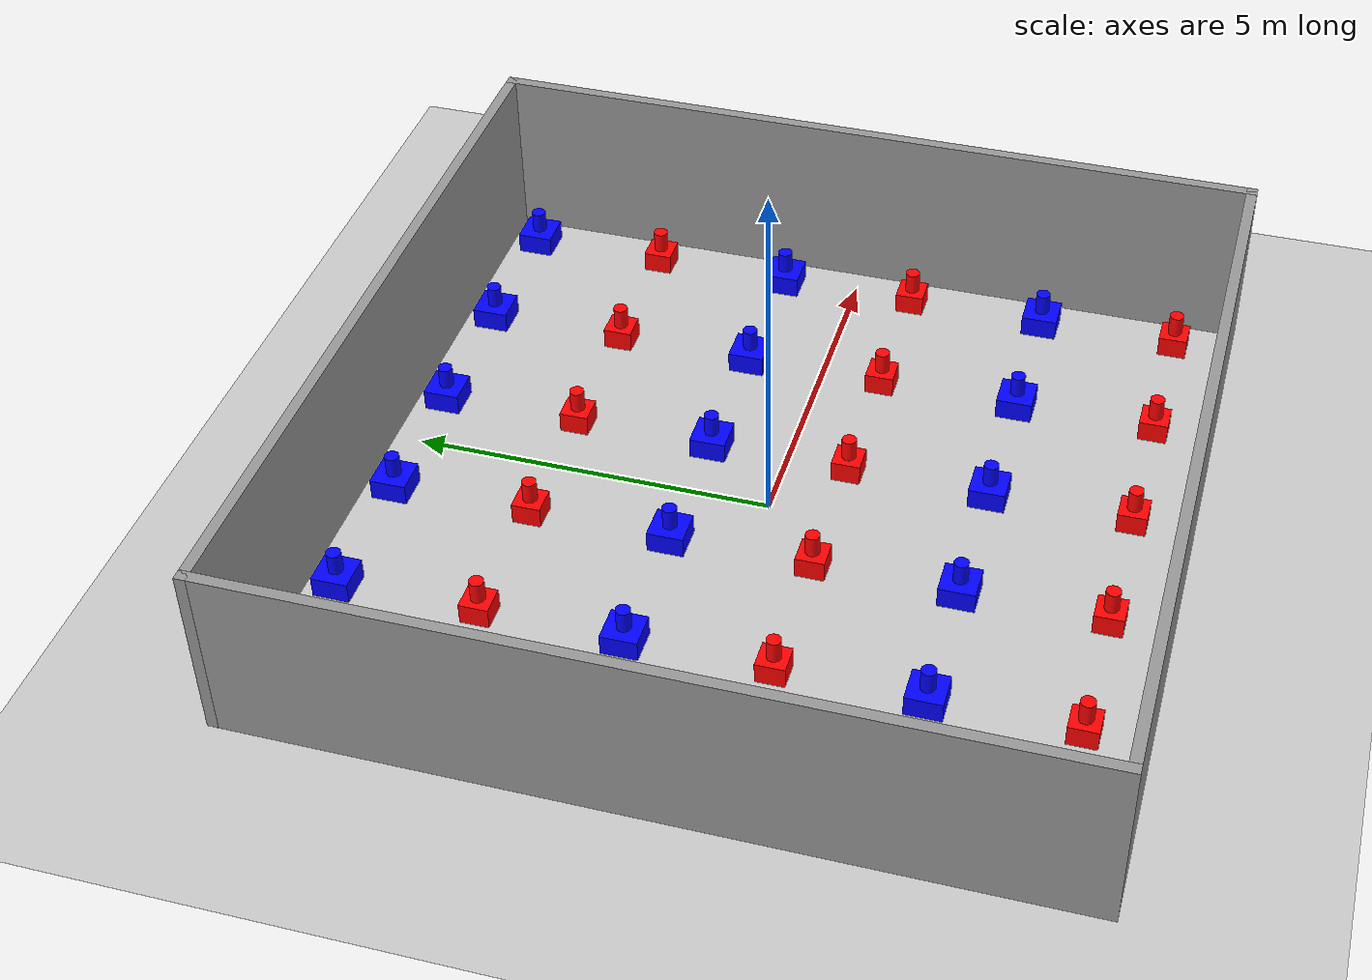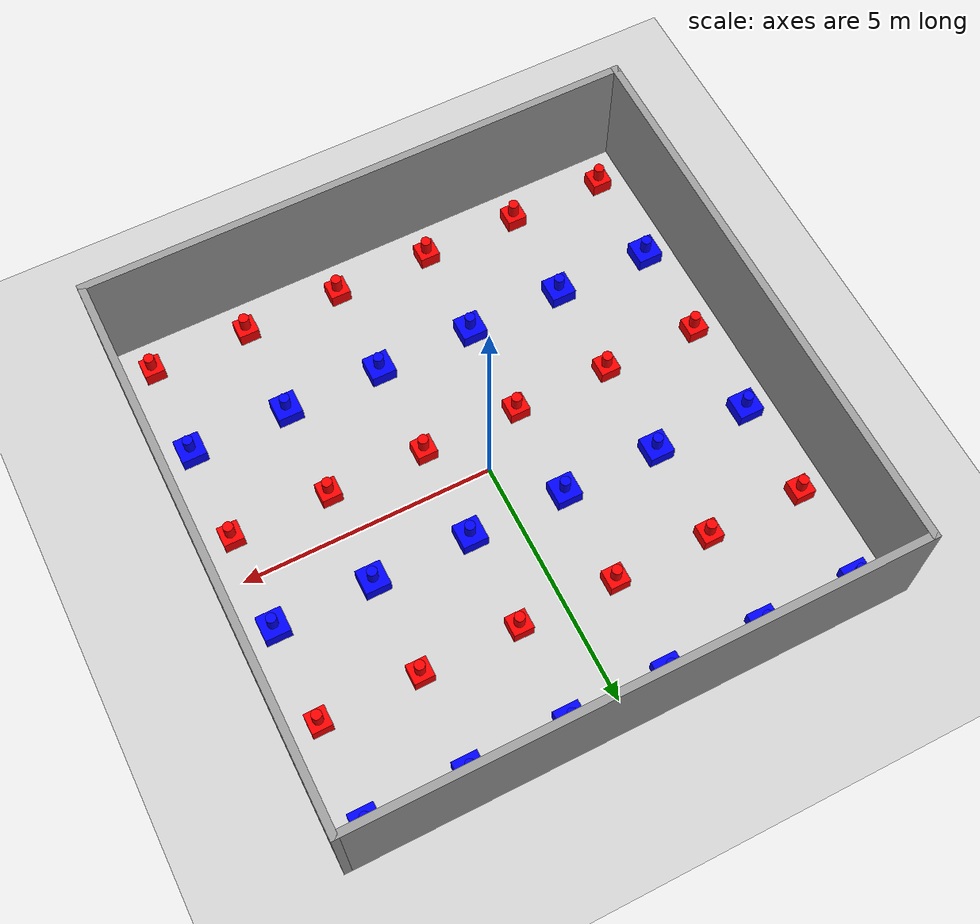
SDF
<sdf version="1.7">
 <world name="default">
  <light name="sun" type="directional">
   <pose>0 0 10 0 -0 0</pose>
   <diffuse>0.8 0.8 0.8 1</diffuse>
   <specular>0.2 0.2 0.2 1</specular>
   <attenuation>
    <range>1000</range>
    <constant>0.9</constant>
    <linear>0.01</linear>
    <quadratic>0.001</quadratic>
   </attenuation>
   <direction>-0.5 0.1 -0.9</direction>
   <spot><inner_angle>0</inner_angle><outer_angle>0</outer_angle><falloff>0</falloff></spot>
  </light>
  <model name="ground_plane">
   <static>1</static>
   <link name="link">
    <collision name="collision">
     <geometry><plane><normal>0 0 1</normal><size>100 100</size></plane></geometry>
     <surface><friction><ode><mu>100</mu><mu2>50</mu2></ode></friction></surface>
    </collision>
    <visual name="visual">
     <cast_shadows>0</cast_shadows>
     <geometry><plane><normal>0 0 1</normal><size>100 100</size></plane></geometry>
     <material>
      <script><uri>file://media/materials/scripts/gazebo.material</uri><name>Gazebo/Grey</name></script>
     </material>
    </visual>
   </link>
  </model>
  <gravity>0 0 -9.8</gravity>
  <magnetic_field>6e-06 2.3e-05 -4.2e-05</magnetic_field>
  <atmosphere type="adiabatic"/>
  <physics type="ode">
   <max_step_size>0.001</max_step_size>
   <real_time_factor>1</real_time_factor>
   <real_time_update_rate>1000</real_time_update_rate>
  </physics>
  <scene><ambient>0.4 0.4 0.4 1</ambient><background>0.7 0.7 0.7 1</background><shadows>1</shadows></scene>
  <spherical_coordinates>
   <surface_model>EARTH_WGS84</surface_model>
   <latitude_deg>0</latitude_deg>
   <longitude_deg>0</longitude_deg>
   <elevation>0</elevation>
   <heading_deg>0</heading_deg>
  </spherical_coordinates>
  <model name="barandwall">
   <model name="bar_net">
    <link name="link_1">
     <inertial>
      <mass>1</mass>
      <inertia><ixx>0.145833</ixx><ixy>0</ixy><ixz>0</ixz><iyy>0.145833</iyy><iyz>0</iyz><izz>0.125</izz></inertia>
     </inertial>
     <pose>-4.87823 -4.8761 0.45 0 -0 0</pose>
     <visual name="visual">
      <geometry><cylinder><radius>0.1</radius><length>0.3</length></cylinder></geometry>
      <material>
       <lighting>1</lighting>
       <script><uri>file://media/materials/scripts/gazebo.material</uri><name>Gazebo/Grey</name></script>
       <shader type="pixel"><normal_map>__default__</normal_map></shader>
       <ambient>1 0 0 1</ambient>
       <diffuse>0.7 0.7 0.7 1</diffuse>
       <specular>0.01 0.01 0.01 1</specular>
       <emissive>0 0 0 1</emissive>
      </material>
     </visual>
     <collision name="collision">
      <geometry><cylinder><radius>0.1</radius><length>0.3</length></cylinder></geometry>
      <surface>
       <friction>
        <ode><mu>1</mu><mu2>1</mu2><fdir1>0 0 0</fdir1><slip1>0</slip1><slip2>0</slip2></ode>
        <torsional>
         <coefficient>1</coefficient>
         <patch_radius>0</patch_radius>
         <surface_radius>0</surface_radius>
         <use_patch_radius>1</use_patch_radius>
         <ode><slip>0</slip></ode>
        </torsional>
       </friction>
       <bounce><restitution_coefficient>0</restitution_coefficient><threshold>1e+06</threshold></bounce>
       <contact>
        <collide_without_contact>0</collide_without_contact>
        <collide_without_contact_bitmask>1</collide_without_contact_bitmask>
        <collide_bitmask>1</collide_bitmask>
        <ode>
         <soft_cfm>0</soft_cfm>
         <soft_erp>0.2</soft_erp>
         <kp>1e+13</kp>
         <kd>1</kd>
         <max_vel>0.01</max_vel>
         <min_depth>0</min_depth>
        </ode>
        <bullet>
         <split_impulse>1</split_impulse>
         <split_impulse_penetration_threshold>-0.01</split_impulse_penetration_threshold>
         <soft_cfm>0</soft_cfm>
         <soft_erp>0.2</soft_erp>
         <kp>1e+13</kp>
         <kd>1</kd>
        </bullet>
       </contact>
      </surface>
     </collision>
    </link>
    <link name="link_1_clone">
     <inertial>
      <mass>1</mass>
      <inertia><ixx>0.145833</ixx><ixy>0</ixy><ixz>0</ixz><iyy>0.145833</iyy><iyz>0</iyz><izz>0.125</izz></inertia>
     </inertial>
     <pose>-4.87823 -2.9261 0.45 0 -0 0</pose>
     <visual name="visual">
      <geometry><cylinder><radius>0.1</radius><length>0.3</length></cylinder></geometry>
      <material>
       <lighting>1</lighting>
       <script><uri>file://media/materials/scripts/gazebo.material</uri><name>Gazebo/Grey</name></script>
       <shader type="pixel"><normal_map>__default__</normal_map></shader>
       <ambient>0 0 1 1</ambient>
       <diffuse>0.7 0.7 0.7 1</diffuse>
       <specular>0.01 0.01 0.01 1</specular>
       <emissive>0 0 0 1</emissive>
      </material>
     </visual>
     <collision name="collision">
      <geometry><cylinder><radius>0.1</radius><length>0.3</length></cylinder></geometry>
      <surface>
       <friction>
        <ode><mu>1</mu><mu2>1</mu2><fdir1>0 0 0</fdir1><slip1>0</slip1><slip2>0</slip2></ode>
        <torsional>
         <coefficient>1</coefficient>
         <patch_radius>0</patch_radius>
         <surface_radius>0</surface_radius>
         <use_patch_radius>1</use_patch_radius>
         <ode><slip>0</slip></ode>
        </torsional>
       </friction>
       <bounce><restitution_coefficient>0</restitution_coefficient><threshold>1e+06</threshold></bounce>
       <contact>
        <collide_without_contact>0</collide_without_contact>
        <collide_without_contact_bitmask>1</collide_without_contact_bitmask>
        <collide_bitmask>1</collide_bitmask>
        <ode>
         <soft_cfm>0</soft_cfm>
         <soft_erp>0.2</soft_erp>
         <kp>1e+13</kp>
         <kd>1</kd>
         <max_vel>0.01</max_vel>
         <min_depth>0</min_depth>
        </ode>
        <bullet>
         <split_impulse>1</split_impulse>
         <split_impulse_penetration_threshold>-0.01</split_impulse_penetration_threshold>
         <soft_cfm>0</soft_cfm>
         <soft_erp>0.2</soft_erp>
         <kp>1e+13</kp>
         <kd>1</kd>
        </bullet>
       </contact>
      </surface>
     </collision>
    </link>
    <link name="link_1_clone_0">
     <inertial>
      <mass>1</mass>
      <inertia><ixx>0.145833</ixx><ixy>0</ixy><ixz>0</ixz><iyy>0.145833</iyy><iyz>0</iyz><izz>0.125</izz></inertia>
     </inertial>
     <pose>-2.92823 -4.8761 0.45 0 -0 0</pose>
     <visual name="visual">
      <geometry><cylinder><radius>0.1</radius><length>0.3</length></cylinder></geometry>
      <material>
       <lighting>1</lighting>
       <script><uri>file://media/materials/scripts/gazebo.material</uri><name>Gazebo/Grey</name></script>
       <shader type="pixel"><normal_map>__default__</normal_map></shader>
       <ambient>1 0 0 1</ambient>
       <diffuse>0.7 0.7 0.7 1</diffuse>
       <specular>0.01 0.01 0.01 1</specular>
       <emissive>0 0 0 1</emissive>
      </material>
     </visual>
     <collision name="collision">
      <geometry><cylinder><radius>0.1</radius><length>0.3</length></cylinder></geometry>
      <surface>
       <friction>
        <ode><mu>1</mu><mu2>1</mu2><fdir1>0 0 0</fdir1><slip1>0</slip1><slip2>0</slip2></ode>
        <torsional>
         <coefficient>1</coefficient>
         <patch_radius>0</patch_radius>
         <surface_radius>0</surface_radius>
         <use_patch_radius>1</use_patch_radius>
         <ode><slip>0</slip></ode>
        </torsional>
       </friction>
       <bounce><restitution_coefficient>0</restitution_coefficient><threshold>1e+06</threshold></bounce>
       <contact>
        <collide_without_contact>0</collide_without_contact>
        <collide_without_contact_bitmask>1</collide_without_contact_bitmask>
        <collide_bitmask>1</collide_bitmask>
        <ode>
         <soft_cfm>0</soft_cfm>
         <soft_erp>0.2</soft_erp>
         <kp>1e+13</kp>
         <kd>1</kd>
         <max_vel>0.01</max_vel>
         <min_depth>0</min_depth>
        </ode>
        <bullet>
         <split_impulse>1</split_impulse>
         <split_impulse_penetration_threshold>-0.01</split_impulse_penetration_threshold>
         <soft_cfm>0</soft_cfm>
         <soft_erp>0.2</soft_erp>
         <kp>1e+13</kp>
         <kd>1</kd>
        </bullet>
       </contact>
      </surface>
     </collision>
    </link>
    <link name="link_1_clone_0_clone">
     <inertial>
      <mass>1</mass>
      <inertia><ixx>0.145833</ixx><ixy>0</ixy><ixz>0</ixz><iyy>0.145833</iyy><iyz>0</iyz><izz>0.125</izz></inertia>
     </inertial>
     <pose>-0.978234 -4.8761 0.45 0 -0 0</pose>
     <visual name="visual">
      <geometry><cylinder><radius>0.1</radius><length>0.3</length></cylinder></geometry>
      <material>
       <lighting>1</lighting>
       <script><uri>file://media/materials/scripts/gazebo.material</uri><name>Gazebo/Grey</name></script>
       <shader type="pixel"><normal_map>__default__</normal_map></shader>
       <ambient>1 0 0 1</ambient>
       <diffuse>0.7 0.7 0.7 1</diffuse>
       <specular>0.01 0.01 0.01 1</specular>
       <emissive>0 0 0 1</emissive>
      </material>
     </visual>
     <collision name="collision">
      <geometry><cylinder><radius>0.1</radius><length>0.3</length></cylinder></geometry>
      <surface>
       <friction>
        <ode><mu>1</mu><mu2>1</mu2><fdir1>0 0 0</fdir1><slip1>0</slip1><slip2>0</slip2></ode>
        <torsional>
         <coefficient>1</coefficient>
         <patch_radius>0</patch_radius>
         <surface_radius>0</surface_radius>
         <use_patch_radius>1</use_patch_radius>
         <ode><slip>0</slip></ode>
        </torsional>
       </friction>
       <bounce><restitution_coefficient>0</restitution_coefficient><threshold>1e+06</threshold></bounce>
       <contact>
        <collide_without_contact>0</collide_without_contact>
        <collide_without_contact_bitmask>1</collide_without_contact_bitmask>
        <collide_bitmask>1</collide_bitmask>
        <ode>
         <soft_cfm>0</soft_cfm>
         <soft_erp>0.2</soft_erp>
         <kp>1e+13</kp>
         <kd>1</kd>
         <max_vel>0.01</max_vel>
         <min_depth>0</min_depth>
        </ode>
        <bullet>
         <split_impulse>1</split_impulse>
         <split_impulse_penetration_threshold>-0.01</split_impulse_penetration_threshold>
         <soft_cfm>0</soft_cfm>
         <soft_erp>0.2</soft_erp>
         <kp>1e+13</kp>
         <kd>1</kd>
        </bullet>
       </contact>
      </surface>
     </collision>
    </link>
    <link name="link_1_clone_0_clone_0">
     <inertial>
      <mass>1</mass>
      <inertia><ixx>0.145833</ixx><ixy>0</ixy><ixz>0</ixz><iyy>0.145833</iyy><iyz>0</iyz><izz>0.125</izz></inertia>
     </inertial>
     <pose>0.971766 -4.8761 0.45 0 -0 0</pose>
     <visual name="visual">
      <geometry><cylinder><radius>0.1</radius><length>0.3</length></cylinder></geometry>
      <material>
       <lighting>1</lighting>
       <script><uri>file://media/materials/scripts/gazebo.material</uri><name>Gazebo/Grey</name></script>
       <shader type="pixel"><normal_map>__default__</normal_map></shader>
       <ambient>1 0 0 1</ambient>
       <diffuse>0.7 0.7 0.7 1</diffuse>
       <specular>0.01 0.01 0.01 1</specular>
       <emissive>0 0 0 1</emissive>
      </material>
     </visual>
     <collision name="collision">
      <geometry><cylinder><radius>0.1</radius><length>0.3</length></cylinder></geometry>
      <surface>
       <friction>
        <ode><mu>1</mu><mu2>1</mu2><fdir1>0 0 0</fdir1><slip1>0</slip1><slip2>0</slip2></ode>
        <torsional>
         <coefficient>1</coefficient>
         <patch_radius>0</patch_radius>
         <surface_radius>0</surface_radius>
         <use_patch_radius>1</use_patch_radius>
         <ode><slip>0</slip></ode>
        </torsional>
       </friction>
       <bounce><restitution_coefficient>0</restitution_coefficient><threshold>1e+06</threshold></bounce>
       <contact>
        <collide_without_contact>0</collide_without_contact>
        <collide_without_contact_bitmask>1</collide_without_contact_bitmask>
        <collide_bitmask>1</collide_bitmask>
        <ode>
         <soft_cfm>0</soft_cfm>
         <soft_erp>0.2</soft_erp>
         <kp>1e+13</kp>
         <kd>1</kd>
         <max_vel>0.01</max_vel>
         <min_depth>0</min_depth>
        </ode>
        <bullet>
         <split_impulse>1</split_impulse>
         <split_impulse_penetration_threshold>-0.01</split_impulse_penetration_threshold>
         <soft_cfm>0</soft_cfm>
         <soft_erp>0.2</soft_erp>
         <kp>1e+13</kp>
         <kd>1</kd>
        </bullet>
       </contact>
      </surface>
     </collision>
    </link>
    <link name="link_1_clone_0_clone_1">
     <inertial>
      <mass>1</mass>
      <inertia><ixx>0.145833</ixx><ixy>0</ixy><ixz>0</ixz><iyy>0.145833</iyy><iyz>0</iyz><izz>0.125</izz></inertia>
     </inertial>
     <pose>2.92177 -4.8761 0.45 0 -0 0</pose>
     <visual name="visual">
      <geometry><cylinder><radius>0.1</radius><length>0.3</length></cylinder></geometry>
      <material>
       <lighting>1</lighting>
       <script><uri>file://media/materials/scripts/gazebo.material</uri><name>Gazebo/Grey</name></script>
       <shader type="pixel"><normal_map>__default__</normal_map></shader>
       <ambient>1 0 0 1</ambient>
       <diffuse>0.7 0.7 0.7 1</diffuse>
       <specular>0.01 0.01 0.01 1</specular>
       <emissive>0 0 0 1</emissive>
      </material>
     </visual>
     <collision name="collision">
      <geometry><cylinder><radius>0.1</radius><length>0.3</length></cylinder></geometry>
      <surface>
       <friction>
        <ode><mu>1</mu><mu2>1</mu2><fdir1>0 0 0</fdir1><slip1>0</slip1><slip2>0</slip2></ode>
        <torsional>
         <coefficient>1</coefficient>
         <patch_radius>0</patch_radius>
         <surface_radius>0</surface_radius>
         <use_patch_radius>1</use_patch_radius>
         <ode><slip>0</slip></ode>
        </torsional>
       </friction>
       <bounce><restitution_coefficient>0</restitution_coefficient><threshold>1e+06</threshold></bounce>
       <contact>
        <collide_without_contact>0</collide_without_contact>
        <collide_without_contact_bitmask>1</collide_without_contact_bitmask>
        <collide_bitmask>1</collide_bitmask>
        <ode>
         <soft_cfm>0</soft_cfm>
         <soft_erp>0.2</soft_erp>
         <kp>1e+13</kp>
         <kd>1</kd>
         <max_vel>0.01</max_vel>
         <min_depth>0</min_depth>
        </ode>
        <bullet>
         <split_impulse>1</split_impulse>
         <split_impulse_penetration_threshold>-0.01</split_impulse_penetration_threshold>
         <soft_cfm>0</soft_cfm>
         <soft_erp>0.2</soft_erp>
         <kp>1e+13</kp>
         <kd>1</kd>
        </bullet>
       </contact>
      </surface>
     </collision>
    </link>
    <link name="link_1_clone_0_clone_2">
     <inertial>
      <mass>1</mass>
      <inertia><ixx>0.145833</ixx><ixy>0</ixy><ixz>0</ixz><iyy>0.145833</iyy><iyz>0</iyz><izz>0.125</izz></inertia>
     </inertial>
     <pose>4.87177 -4.8761 0.45 0 -0 0</pose>
     <visual name="visual">
      <geometry><cylinder><radius>0.1</radius><length>0.3</length></cylinder></geometry>
      <material>
       <lighting>1</lighting>
       <script><uri>file://media/materials/scripts/gazebo.material</uri><name>Gazebo/Grey</name></script>
       <shader type="pixel"><normal_map>__default__</normal_map></shader>
       <ambient>1 0 0 1</ambient>
       <diffuse>0.7 0.7 0.7 1</diffuse>
       <specular>0.01 0.01 0.01 1</specular>
       <emissive>0 0 0 1</emissive>
      </material>
     </visual>
     <collision name="collision">
      <geometry><cylinder><radius>0.1</radius><length>0.3</length></cylinder></geometry>
      <surface>
       <friction>
        <ode><mu>1</mu><mu2>1</mu2><fdir1>0 0 0</fdir1><slip1>0</slip1><slip2>0</slip2></ode>
        <torsional>
         <coefficient>1</coefficient>
         <patch_radius>0</patch_radius>
         <surface_radius>0</surface_radius>
         <use_patch_radius>1</use_patch_radius>
         <ode><slip>0</slip></ode>
        </torsional>
       </friction>
       <bounce><restitution_coefficient>0</restitution_coefficient><threshold>1e+06</threshold></bounce>
       <contact>
        <collide_without_contact>0</collide_without_contact>
        <collide_without_contact_bitmask>1</collide_without_contact_bitmask>
        <collide_bitmask>1</collide_bitmask>
        <ode>
         <soft_cfm>0</soft_cfm>
         <soft_erp>0.2</soft_erp>
         <kp>1e+13</kp>
         <kd>1</kd>
         <max_vel>0.01</max_vel>
         <min_depth>0</min_depth>
        </ode>
        <bullet>
         <split_impulse>1</split_impulse>
         <split_impulse_penetration_threshold>-0.01</split_impulse_penetration_threshold>
         <soft_cfm>0</soft_cfm>
         <soft_erp>0.2</soft_erp>
         <kp>1e+13</kp>
         <kd>1</kd>
        </bullet>
       </contact>
      </surface>
     </collision>
    </link>
    <link name="link_1_clone_1">
     <inertial>
      <mass>1</mass>
      <inertia><ixx>0.145833</ixx><ixy>0</ixy><ixz>0</ixz><iyy>0.145833</iyy><iyz>0</iyz><izz>0.125</izz></inertia>
     </inertial>
     <pose>-4.87014 -0.986599 0.45 0 -0 0</pose>
     <visual name="visual">
      <geometry><cylinder><radius>0.1</radius><length>0.3</length></cylinder></geometry>
      <material>
       <lighting>1</lighting>
       <script><uri>file://media/materials/scripts/gazebo.material</uri><name>Gazebo/Grey</name></script>
       <shader type="pixel"><normal_map>__default__</normal_map></shader>
       <ambient>1 0 0 1</ambient>
       <diffuse>0.7 0.7 0.7 1</diffuse>
       <specular>0.01 0.01 0.01 1</specular>
       <emissive>0 0 0 1</emissive>
      </material>
     </visual>
     <collision name="collision">
      <geometry><cylinder><radius>0.1</radius><length>0.3</length></cylinder></geometry>
      <surface>
       <friction>
        <ode><mu>1</mu><mu2>1</mu2><fdir1>0 0 0</fdir1><slip1>0</slip1><slip2>0</slip2></ode>
        <torsional>
         <coefficient>1</coefficient>
         <patch_radius>0</patch_radius>
         <surface_radius>0</surface_radius>
         <use_patch_radius>1</use_patch_radius>
         <ode><slip>0</slip></ode>
        </torsional>
       </friction>
       <bounce><restitution_coefficient>0</restitution_coefficient><threshold>1e+06</threshold></bounce>
       <contact>
        <collide_without_contact>0</collide_without_contact>
        <collide_without_contact_bitmask>1</collide_without_contact_bitmask>
        <collide_bitmask>1</collide_bitmask>
        <ode>
         <soft_cfm>0</soft_cfm>
         <soft_erp>0.2</soft_erp>
         <kp>1e+13</kp>
         <kd>1</kd>
         <max_vel>0.01</max_vel>
         <min_depth>0</min_depth>
        </ode>
        <bullet>
         <split_impulse>1</split_impulse>
         <split_impulse_penetration_threshold>-0.01</split_impulse_penetration_threshold>
         <soft_cfm>0</soft_cfm>
         <soft_erp>0.2</soft_erp>
         <kp>1e+13</kp>
         <kd>1</kd>
        </bullet>
       </contact>
      </surface>
     </collision>
    </link>
    <link name="link_1_clone_10">
     <inertial>
      <mass>1</mass>
      <inertia><ixx>0.145833</ixx><ixy>0</ixy><ixz>0</ixz><iyy>0.145833</iyy><iyz>0</iyz><izz>0.125</izz></inertia>
     </inertial>
     <pose>0.971766 2.9239 0.45 0 -0 0</pose>
     <visual name="visual">
      <geometry><cylinder><radius>0.1</radius><length>0.3</length></cylinder></geometry>
      <material>
       <lighting>1</lighting>
       <script><uri>file://media/materials/scripts/gazebo.material</uri><name>Gazebo/Grey</name></script>
       <shader type="pixel"><normal_map>__default__</normal_map></shader>
       <ambient>1 0 0 1</ambient>
       <diffuse>0.7 0.7 0.7 1</diffuse>
       <specular>0.01 0.01 0.01 1</specular>
       <emissive>0 0 0 1</emissive>
      </material>
     </visual>
     <collision name="collision">
      <geometry><cylinder><radius>0.1</radius><length>0.3</length></cylinder></geometry>
      <surface>
       <friction>
        <ode><mu>1</mu><mu2>1</mu2><fdir1>0 0 0</fdir1><slip1>0</slip1><slip2>0</slip2></ode>
        <torsional>
         <coefficient>1</coefficient>
         <patch_radius>0</patch_radius>
         <surface_radius>0</surface_radius>
         <use_patch_radius>1</use_patch_radius>
         <ode><slip>0</slip></ode>
        </torsional>
       </friction>
       <bounce><restitution_coefficient>0</restitution_coefficient><threshold>1e+06</threshold></bounce>
       <contact>
        <collide_without_contact>0</collide_without_contact>
        <collide_without_contact_bitmask>1</collide_without_contact_bitmask>
        <collide_bitmask>1</collide_bitmask>
        <ode>
         <soft_cfm>0</soft_cfm>
         <soft_erp>0.2</soft_erp>
         <kp>1e+13</kp>
         <kd>1</kd>
         <max_vel>0.01</max_vel>
         <min_depth>0</min_depth>
        </ode>
        <bullet>
         <split_impulse>1</split_impulse>
         <split_impulse_penetration_threshold>-0.01</split_impulse_penetration_threshold>
         <soft_cfm>0</soft_cfm>
         <soft_erp>0.2</soft_erp>
         <kp>1e+13</kp>
         <kd>1</kd>
        </bullet>
       </contact>
      </surface>
     </collision>
    </link>
    <link name="link_1_clone_11">
     <inertial>
      <mass>1</mass>
      <inertia><ixx>0.145833</ixx><ixy>0</ixy><ixz>0</ixz><iyy>0.145833</iyy><iyz>0</iyz><izz>0.125</izz></inertia>
     </inertial>
     <pose>2.92177 2.9239 0.45 0 -0 0</pose>
     <visual name="visual">
      <geometry><cylinder><radius>0.1</radius><length>0.3</length></cylinder></geometry>
      <material>
       <lighting>1</lighting>
       <script><uri>file://media/materials/scripts/gazebo.material</uri><name>Gazebo/Grey</name></script>
       <shader type="pixel"><normal_map>__default__</normal_map></shader>
       <ambient>1 0 0 1</ambient>
       <diffuse>0.7 0.7 0.7 1</diffuse>
       <specular>0.01 0.01 0.01 1</specular>
       <emissive>0 0 0 1</emissive>
      </material>
     </visual>
     <collision name="collision">
      <geometry><cylinder><radius>0.1</radius><length>0.3</length></cylinder></geometry>
      <surface>
       <friction>
        <ode><mu>1</mu><mu2>1</mu2><fdir1>0 0 0</fdir1><slip1>0</slip1><slip2>0</slip2></ode>
        <torsional>
         <coefficient>1</coefficient>
         <patch_radius>0</patch_radius>
         <surface_radius>0</surface_radius>
         <use_patch_radius>1</use_patch_radius>
         <ode><slip>0</slip></ode>
        </torsional>
       </friction>
       <bounce><restitution_coefficient>0</restitution_coefficient><threshold>1e+06</threshold></bounce>
       <contact>
        <collide_without_contact>0</collide_without_contact>
        <collide_without_contact_bitmask>1</collide_without_contact_bitmask>
        <collide_bitmask>1</collide_bitmask>
        <ode>
         <soft_cfm>0</soft_cfm>
         <soft_erp>0.2</soft_erp>
         <kp>1e+13</kp>
         <kd>1</kd>
         <max_vel>0.01</max_vel>
         <min_depth>0</min_depth>
        </ode>
        <bullet>
         <split_impulse>1</split_impulse>
         <split_impulse_penetration_threshold>-0.01</split_impulse_penetration_threshold>
         <soft_cfm>0</soft_cfm>
         <soft_erp>0.2</soft_erp>
         <kp>1e+13</kp>
         <kd>1</kd>
        </bullet>
       </contact>
      </surface>
     </collision>
    </link>
    <link name="link_1_clone_12">
     <inertial>
      <mass>1</mass>
      <inertia><ixx>0.145833</ixx><ixy>0</ixy><ixz>0</ixz><iyy>0.145833</iyy><iyz>0</iyz><izz>0.125</izz></inertia>
     </inertial>
     <pose>4.87177 2.9239 0.45 0 -0 0</pose>
     <visual name="visual">
      <geometry><cylinder><radius>0.1</radius><length>0.3</length></cylinder></geometry>
      <material>
       <lighting>1</lighting>
       <script><uri>file://media/materials/scripts/gazebo.material</uri><name>Gazebo/Grey</name></script>
       <shader type="pixel"><normal_map>__default__</normal_map></shader>
       <ambient>1 0 0 1</ambient>
       <diffuse>0.7 0.7 0.7 1</diffuse>
       <specular>0.01 0.01 0.01 1</specular>
       <emissive>0 0 0 1</emissive>
      </material>
     </visual>
     <collision name="collision">
      <geometry><cylinder><radius>0.1</radius><length>0.3</length></cylinder></geometry>
      <surface>
       <friction>
        <ode><mu>1</mu><mu2>1</mu2><fdir1>0 0 0</fdir1><slip1>0</slip1><slip2>0</slip2></ode>
        <torsional>
         <coefficient>1</coefficient>
         <patch_radius>0</patch_radius>
         <surface_radius>0</surface_radius>
         <use_patch_radius>1</use_patch_radius>
         <ode><slip>0</slip></ode>
        </torsional>
       </friction>
       <bounce><restitution_coefficient>0</restitution_coefficient><threshold>1e+06</threshold></bounce>
       <contact>
        <collide_without_contact>0</collide_without_contact>
        <collide_without_contact_bitmask>1</collide_without_contact_bitmask>
        <collide_bitmask>1</collide_bitmask>
        <ode>
         <soft_cfm>0</soft_cfm>
         <soft_erp>0.2</soft_erp>
         <kp>1e+13</kp>
         <kd>1</kd>
         <max_vel>0.01</max_vel>
         <min_depth>0</min_depth>
        </ode>
        <bullet>
         <split_impulse>1</split_impulse>
         <split_impulse_penetration_threshold>-0.01</split_impulse_penetration_threshold>
         <soft_cfm>0</soft_cfm>
         <soft_erp>0.2</soft_erp>
         <kp>1e+13</kp>
         <kd>1</kd>
        </bullet>
       </contact>
      </surface>
     </collision>
    </link>
    <link name="link_1_clone_2">
     <inertial>
      <mass>1</mass>
      <inertia><ixx>0.145833</ixx><ixy>0</ixy><ixz>0</ixz><iyy>0.145833</iyy><iyz>0</iyz><izz>0.125</izz></inertia>
     </inertial>
     <pose>-2.92823 -0.9761 0.45 0 -0 0</pose>
     <visual name="visual">
      <geometry><cylinder><radius>0.1</radius><length>0.3</length></cylinder></geometry>
      <material>
       <lighting>1</lighting>
       <script><uri>file://media/materials/scripts/gazebo.material</uri><name>Gazebo/Grey</name></script>
       <shader type="pixel"><normal_map>__default__</normal_map></shader>
       <ambient>1 0 0 1</ambient>
       <diffuse>0.7 0.7 0.7 1</diffuse>
       <specular>0.01 0.01 0.01 1</specular>
       <emissive>0 0 0 1</emissive>
      </material>
     </visual>
     <collision name="collision">
      <geometry><cylinder><radius>0.1</radius><length>0.3</length></cylinder></geometry>
      <surface>
       <friction>
        <ode><mu>1</mu><mu2>1</mu2><fdir1>0 0 0</fdir1><slip1>0</slip1><slip2>0</slip2></ode>
        <torsional>
         <coefficient>1</coefficient>
         <patch_radius>0</patch_radius>
         <surface_radius>0</surface_radius>
         <use_patch_radius>1</use_patch_radius>
         <ode><slip>0</slip></ode>
        </torsional>
       </friction>
       <bounce><restitution_coefficient>0</restitution_coefficient><threshold>1e+06</threshold></bounce>
       <contact>
        <collide_without_contact>0</collide_without_contact>
        <collide_without_contact_bitmask>1</collide_without_contact_bitmask>
        <collide_bitmask>1</collide_bitmask>
        <ode>
         <soft_cfm>0</soft_cfm>
         <soft_erp>0.2</soft_erp>
         <kp>1e+13</kp>
         <kd>1</kd>
         <max_vel>0.01</max_vel>
         <min_depth>0</min_depth>
        </ode>
        <bullet>
         <split_impulse>1</split_impulse>
         <split_impulse_penetration_threshold>-0.01</split_impulse_penetration_threshold>
         <soft_cfm>0</soft_cfm>
         <soft_erp>0.2</soft_erp>
         <kp>1e+13</kp>
         <kd>1</kd>
        </bullet>
       </contact>
      </surface>
     </collision>
    </link>
    <link name="link_1_clone_3">
     <inertial>
      <mass>1</mass>
      <inertia><ixx>0.145833</ixx><ixy>0</ixy><ixz>0</ixz><iyy>0.145833</iyy><iyz>0</iyz><izz>0.125</izz></inertia>
     </inertial>
     <pose>-0.979901 -0.965591 0.45 0 -0 0</pose>
     <visual name="visual">
      <geometry><cylinder><radius>0.1</radius><length>0.3</length></cylinder></geometry>
      <material>
       <lighting>1</lighting>
       <script><uri>file://media/materials/scripts/gazebo.material</uri><name>Gazebo/Grey</name></script>
       <shader type="pixel"><normal_map>__default__</normal_map></shader>
       <ambient>1 0 0 1</ambient>
       <diffuse>0.7 0.7 0.7 1</diffuse>
       <specular>0.01 0.01 0.01 1</specular>
       <emissive>0 0 0 1</emissive>
      </material>
     </visual>
     <collision name="collision">
      <geometry><cylinder><radius>0.1</radius><length>0.3</length></cylinder></geometry>
      <surface>
       <friction>
        <ode><mu>1</mu><mu2>1</mu2><fdir1>0 0 0</fdir1><slip1>0</slip1><slip2>0</slip2></ode>
        <torsional>
         <coefficient>1</coefficient>
         <patch_radius>0</patch_radius>
         <surface_radius>0</surface_radius>
         <use_patch_radius>1</use_patch_radius>
         <ode><slip>0</slip></ode>
        </torsional>
       </friction>
       <bounce><restitution_coefficient>0</restitution_coefficient><threshold>1e+06</threshold></bounce>
       <contact>
        <collide_without_contact>0</collide_without_contact>
        <collide_without_contact_bitmask>1</collide_without_contact_bitmask>
        <collide_bitmask>1</collide_bitmask>
        <ode>
         <soft_cfm>0</soft_cfm>
         <soft_erp>0.2</soft_erp>
         <kp>1e+13</kp>
         <kd>1</kd>
         <max_vel>0.01</max_vel>
         <min_depth>0</min_depth>
        </ode>
        <bullet>
         <split_impulse>1</split_impulse>
         <split_impulse_penetration_threshold>-0.01</split_impulse_penetration_threshold>
         <soft_cfm>0</soft_cfm>
         <soft_erp>0.2</soft_erp>
         <kp>1e+13</kp>
         <kd>1</kd>
        </bullet>
       </contact>
      </surface>
     </collision>
    </link>
    <link name="link_1_clone_4">
     <inertial>
      <mass>1</mass>
      <inertia><ixx>0.145833</ixx><ixy>0</ixy><ixz>0</ixz><iyy>0.145833</iyy><iyz>0</iyz><izz>0.125</izz></inertia>
     </inertial>
     <pose>0.971766 -0.969525 0.45 0 -0 0</pose>
     <visual name="visual">
      <geometry><cylinder><radius>0.1</radius><length>0.3</length></cylinder></geometry>
      <material>
       <lighting>1</lighting>
       <script><uri>file://media/materials/scripts/gazebo.material</uri><name>Gazebo/Grey</name></script>
       <shader type="pixel"><normal_map>__default__</normal_map></shader>
       <ambient>1 0 0 1</ambient>
       <diffuse>0.7 0.7 0.7 1</diffuse>
       <specular>0.01 0.01 0.01 1</specular>
       <emissive>0 0 0 1</emissive>
      </material>
     </visual>
     <collision name="collision">
      <geometry><cylinder><radius>0.1</radius><length>0.3</length></cylinder></geometry>
      <surface>
       <friction>
        <ode><mu>1</mu><mu2>1</mu2><fdir1>0 0 0</fdir1><slip1>0</slip1><slip2>0</slip2></ode>
        <torsional>
         <coefficient>1</coefficient>
         <patch_radius>0</patch_radius>
         <surface_radius>0</surface_radius>
         <use_patch_radius>1</use_patch_radius>
         <ode><slip>0</slip></ode>
        </torsional>
       </friction>
       <bounce><restitution_coefficient>0</restitution_coefficient><threshold>1e+06</threshold></bounce>
       <contact>
        <collide_without_contact>0</collide_without_contact>
        <collide_without_contact_bitmask>1</collide_without_contact_bitmask>
        <collide_bitmask>1</collide_bitmask>
        <ode>
         <soft_cfm>0</soft_cfm>
         <soft_erp>0.2</soft_erp>
         <kp>1e+13</kp>
         <kd>1</kd>
         <max_vel>0.01</max_vel>
         <min_depth>0</min_depth>
        </ode>
        <bullet>
         <split_impulse>1</split_impulse>
         <split_impulse_penetration_threshold>-0.01</split_impulse_penetration_threshold>
         <soft_cfm>0</soft_cfm>
         <soft_erp>0.2</soft_erp>
         <kp>1e+13</kp>
         <kd>1</kd>
        </bullet>
       </contact>
      </surface>
     </collision>
    </link>
    <link name="link_1_clone_5">
     <inertial>
      <mass>1</mass>
      <inertia><ixx>0.145833</ixx><ixy>0</ixy><ixz>0</ixz><iyy>0.145833</iyy><iyz>0</iyz><izz>0.125</izz></inertia>
     </inertial>
     <pose>2.92177 -0.9761 0.45 0 -0 0</pose>
     <visual name="visual">
      <geometry><cylinder><radius>0.1</radius><length>0.3</length></cylinder></geometry>
      <material>
       <lighting>1</lighting>
       <script><uri>file://media/materials/scripts/gazebo.material</uri><name>Gazebo/Grey</name></script>
       <shader type="pixel"><normal_map>__default__</normal_map></shader>
       <ambient>1 0 0 1</ambient>
       <diffuse>0.7 0.7 0.7 1</diffuse>
       <specular>0.01 0.01 0.01 1</specular>
       <emissive>0 0 0 1</emissive>
      </material>
     </visual>
     <collision name="collision">
      <geometry><cylinder><radius>0.1</radius><length>0.3</length></cylinder></geometry>
      <surface>
       <friction>
        <ode><mu>1</mu><mu2>1</mu2><fdir1>0 0 0</fdir1><slip1>0</slip1><slip2>0</slip2></ode>
        <torsional>
         <coefficient>1</coefficient>
         <patch_radius>0</patch_radius>
         <surface_radius>0</surface_radius>
         <use_patch_radius>1</use_patch_radius>
         <ode><slip>0</slip></ode>
        </torsional>
       </friction>
       <bounce><restitution_coefficient>0</restitution_coefficient><threshold>1e+06</threshold></bounce>
       <contact>
        <collide_without_contact>0</collide_without_contact>
        <collide_without_contact_bitmask>1</collide_without_contact_bitmask>
        <collide_bitmask>1</collide_bitmask>
        <ode>
         <soft_cfm>0</soft_cfm>
         <soft_erp>0.2</soft_erp>
         <kp>1e+13</kp>
         <kd>1</kd>
         <max_vel>0.01</max_vel>
         <min_depth>0</min_depth>
        </ode>
        <bullet>
         <split_impulse>1</split_impulse>
         <split_impulse_penetration_threshold>-0.01</split_impulse_penetration_threshold>
         <soft_cfm>0</soft_cfm>
         <soft_erp>0.2</soft_erp>
         <kp>1e+13</kp>
         <kd>1</kd>
        </bullet>
       </contact>
      </surface>
     </collision>
    </link>
    <link name="link_1_clone_6">
     <inertial>
      <mass>1</mass>
      <inertia><ixx>0.145833</ixx><ixy>0</ixy><ixz>0</ixz><iyy>0.145833</iyy><iyz>0</iyz><izz>0.125</izz></inertia>
     </inertial>
     <pose>4.87177 -0.9761 0.45 0 -0 0</pose>
     <visual name="visual">
      <geometry><cylinder><radius>0.1</radius><length>0.3</length></cylinder></geometry>
      <material>
       <lighting>1</lighting>
       <script><uri>file://media/materials/scripts/gazebo.material</uri><name>Gazebo/Grey</name></script>
       <shader type="pixel"><normal_map>__default__</normal_map></shader>
       <ambient>1 0 0 1</ambient>
       <diffuse>0.7 0.7 0.7 1</diffuse>
       <specular>0.01 0.01 0.01 1</specular>
       <emissive>0 0 0 1</emissive>
      </material>
     </visual>
     <collision name="collision">
      <geometry><cylinder><radius>0.1</radius><length>0.3</length></cylinder></geometry>
      <surface>
       <friction>
        <ode><mu>1</mu><mu2>1</mu2><fdir1>0 0 0</fdir1><slip1>0</slip1><slip2>0</slip2></ode>
        <torsional>
         <coefficient>1</coefficient>
         <patch_radius>0</patch_radius>
         <surface_radius>0</surface_radius>
         <use_patch_radius>1</use_patch_radius>
         <ode><slip>0</slip></ode>
        </torsional>
       </friction>
       <bounce><restitution_coefficient>0</restitution_coefficient><threshold>1e+06</threshold></bounce>
       <contact>
        <collide_without_contact>0</collide_without_contact>
        <collide_without_contact_bitmask>1</collide_without_contact_bitmask>
        <collide_bitmask>1</collide_bitmask>
        <ode>
         <soft_cfm>0</soft_cfm>
         <soft_erp>0.2</soft_erp>
         <kp>1e+13</kp>
         <kd>1</kd>
         <max_vel>0.01</max_vel>
         <min_depth>0</min_depth>
        </ode>
        <bullet>
         <split_impulse>1</split_impulse>
         <split_impulse_penetration_threshold>-0.01</split_impulse_penetration_threshold>
         <soft_cfm>0</soft_cfm>
         <soft_erp>0.2</soft_erp>
         <kp>1e+13</kp>
         <kd>1</kd>
        </bullet>
       </contact>
      </surface>
     </collision>
    </link>
    <link name="link_1_clone_7">
     <inertial>
      <mass>1</mass>
      <inertia><ixx>0.145833</ixx><ixy>0</ixy><ixz>0</ixz><iyy>0.145833</iyy><iyz>0</iyz><izz>0.125</izz></inertia>
     </inertial>
     <pose>-4.87823 2.9239 0.45 0 -0 0</pose>
     <visual name="visual">
      <geometry><cylinder><radius>0.1</radius><length>0.3</length></cylinder></geometry>
      <material>
       <lighting>1</lighting>
       <script><uri>file://media/materials/scripts/gazebo.material</uri><name>Gazebo/Grey</name></script>
       <shader type="pixel"><normal_map>__default__</normal_map></shader>
       <ambient>1 0 0 1</ambient>
       <diffuse>0.7 0.7 0.7 1</diffuse>
       <specular>0.01 0.01 0.01 1</specular>
       <emissive>0 0 0 1</emissive>
      </material>
     </visual>
     <collision name="collision">
      <geometry><cylinder><radius>0.1</radius><length>0.3</length></cylinder></geometry>
      <surface>
       <friction>
        <ode><mu>1</mu><mu2>1</mu2><fdir1>0 0 0</fdir1><slip1>0</slip1><slip2>0</slip2></ode>
        <torsional>
         <coefficient>1</coefficient>
         <patch_radius>0</patch_radius>
         <surface_radius>0</surface_radius>
         <use_patch_radius>1</use_patch_radius>
         <ode><slip>0</slip></ode>
        </torsional>
       </friction>
       <bounce><restitution_coefficient>0</restitution_coefficient><threshold>1e+06</threshold></bounce>
       <contact>
        <collide_without_contact>0</collide_without_contact>
        <collide_without_contact_bitmask>1</collide_without_contact_bitmask>
        <collide_bitmask>1</collide_bitmask>
        <ode>
         <soft_cfm>0</soft_cfm>
         <soft_erp>0.2</soft_erp>
         <kp>1e+13</kp>
         <kd>1</kd>
         <max_vel>0.01</max_vel>
         <min_depth>0</min_depth>
        </ode>
        <bullet>
         <split_impulse>1</split_impulse>
         <split_impulse_penetration_threshold>-0.01</split_impulse_penetration_threshold>
         <soft_cfm>0</soft_cfm>
         <soft_erp>0.2</soft_erp>
         <kp>1e+13</kp>
         <kd>1</kd>
        </bullet>
       </contact>
      </surface>
     </collision>
    </link>
    <link name="link_1_clone_8">
     <inertial>
      <mass>1</mass>
      <inertia><ixx>0.145833</ixx><ixy>0</ixy><ixz>0</ixz><iyy>0.145833</iyy><iyz>0</iyz><izz>0.125</izz></inertia>
     </inertial>
     <pose>-2.92823 2.9239 0.45 0 -0 0</pose>
     <visual name="visual">
      <geometry><cylinder><radius>0.1</radius><length>0.3</length></cylinder></geometry>
      <material>
       <lighting>1</lighting>
       <script><uri>file://media/materials/scripts/gazebo.material</uri><name>Gazebo/Grey</name></script>
       <shader type="pixel"><normal_map>__default__</normal_map></shader>
       <ambient>1 0 0 1</ambient>
       <diffuse>0.7 0.7 0.7 1</diffuse>
       <specular>0.01 0.01 0.01 1</specular>
       <emissive>0 0 0 1</emissive>
      </material>
     </visual>
     <collision name="collision">
      <geometry><cylinder><radius>0.1</radius><length>0.3</length></cylinder></geometry>
      <surface>
       <friction>
        <ode><mu>1</mu><mu2>1</mu2><fdir1>0 0 0</fdir1><slip1>0</slip1><slip2>0</slip2></ode>
        <torsional>
         <coefficient>1</coefficient>
         <patch_radius>0</patch_radius>
         <surface_radius>0</surface_radius>
         <use_patch_radius>1</use_patch_radius>
         <ode><slip>0</slip></ode>
        </torsional>
       </friction>
       <bounce><restitution_coefficient>0</restitution_coefficient><threshold>1e+06</threshold></bounce>
       <contact>
        <collide_without_contact>0</collide_without_contact>
        <collide_without_contact_bitmask>1</collide_without_contact_bitmask>
        <collide_bitmask>1</collide_bitmask>
        <ode>
         <soft_cfm>0</soft_cfm>
         <soft_erp>0.2</soft_erp>
         <kp>1e+13</kp>
         <kd>1</kd>
         <max_vel>0.01</max_vel>
         <min_depth>0</min_depth>
        </ode>
        <bullet>
         <split_impulse>1</split_impulse>
         <split_impulse_penetration_threshold>-0.01</split_impulse_penetration_threshold>
         <soft_cfm>0</soft_cfm>
         <soft_erp>0.2</soft_erp>
         <kp>1e+13</kp>
         <kd>1</kd>
        </bullet>
       </contact>
      </surface>
     </collision>
    </link>
    <link name="link_1_clone_9">
     <inertial>
      <mass>1</mass>
      <inertia><ixx>0.145833</ixx><ixy>0</ixy><ixz>0</ixz><iyy>0.145833</iyy><iyz>0</iyz><izz>0.125</izz></inertia>
     </inertial>
     <pose>-0.978234 2.9239 0.45 0 -0 0</pose>
     <visual name="visual">
      <geometry><cylinder><radius>0.1</radius><length>0.3</length></cylinder></geometry>
      <material>
       <lighting>1</lighting>
       <script><uri>file://media/materials/scripts/gazebo.material</uri><name>Gazebo/Grey</name></script>
       <shader type="pixel"><normal_map>__default__</normal_map></shader>
       <ambient>1 0 0 1</ambient>
       <diffuse>0.7 0.7 0.7 1</diffuse>
       <specular>0.01 0.01 0.01 1</specular>
       <emissive>0 0 0 1</emissive>
      </material>
     </visual>
     <collision name="collision">
      <geometry><cylinder><radius>0.1</radius><length>0.3</length></cylinder></geometry>
      <surface>
       <friction>
        <ode><mu>1</mu><mu2>1</mu2><fdir1>0 0 0</fdir1><slip1>0</slip1><slip2>0</slip2></ode>
        <torsional>
         <coefficient>1</coefficient>
         <patch_radius>0</patch_radius>
         <surface_radius>0</surface_radius>
         <use_patch_radius>1</use_patch_radius>
         <ode><slip>0</slip></ode>
        </torsional>
       </friction>
       <bounce><restitution_coefficient>0</restitution_coefficient><threshold>1e+06</threshold></bounce>
       <contact>
        <collide_without_contact>0</collide_without_contact>
        <collide_without_contact_bitmask>1</collide_without_contact_bitmask>
        <collide_bitmask>1</collide_bitmask>
        <ode>
         <soft_cfm>0</soft_cfm>
         <soft_erp>0.2</soft_erp>
         <kp>1e+13</kp>
         <kd>1</kd>
         <max_vel>0.01</max_vel>
         <min_depth>0</min_depth>
        </ode>
        <bullet>
         <split_impulse>1</split_impulse>
         <split_impulse_penetration_threshold>-0.01</split_impulse_penetration_threshold>
         <soft_cfm>0</soft_cfm>
         <soft_erp>0.2</soft_erp>
         <kp>1e+13</kp>
         <kd>1</kd>
        </bullet>
       </contact>
      </surface>
     </collision>
    </link>
    <link name="link_1_clone_clone">
     <inertial>
      <mass>1</mass>
      <inertia><ixx>0.145833</ixx><ixy>0</ixy><ixz>0</ixz><iyy>0.145833</iyy><iyz>0</iyz><izz>0.125</izz></inertia>
     </inertial>
     <pose>-2.92823 -2.9261 0.45 0 -0 0</pose>
     <visual name="visual">
      <geometry><cylinder><radius>0.1</radius><length>0.3</length></cylinder></geometry>
      <material>
       <lighting>1</lighting>
       <script><uri>file://media/materials/scripts/gazebo.material</uri><name>Gazebo/Grey</name></script>
       <shader type="pixel"><normal_map>__default__</normal_map></shader>
       <ambient>0 0 1 1</ambient>
       <diffuse>0.7 0.7 0.7 1</diffuse>
       <specular>0.01 0.01 0.01 1</specular>
       <emissive>0 0 0 1</emissive>
      </material>
     </visual>
     <collision name="collision">
      <geometry><cylinder><radius>0.1</radius><length>0.3</length></cylinder></geometry>
      <surface>
       <friction>
        <ode><mu>1</mu><mu2>1</mu2><fdir1>0 0 0</fdir1><slip1>0</slip1><slip2>0</slip2></ode>
        <torsional>
         <coefficient>1</coefficient>
         <patch_radius>0</patch_radius>
         <surface_radius>0</surface_radius>
         <use_patch_radius>1</use_patch_radius>
         <ode><slip>0</slip></ode>
        </torsional>
       </friction>
       <bounce><restitution_coefficient>0</restitution_coefficient><threshold>1e+06</threshold></bounce>
       <contact>
        <collide_without_contact>0</collide_without_contact>
        <collide_without_contact_bitmask>1</collide_without_contact_bitmask>
        <collide_bitmask>1</collide_bitmask>
        <ode>
         <soft_cfm>0</soft_cfm>
         <soft_erp>0.2</soft_erp>
         <kp>1e+13</kp>
         <kd>1</kd>
         <max_vel>0.01</max_vel>
         <min_depth>0</min_depth>
        </ode>
        <bullet>
         <split_impulse>1</split_impulse>
         <split_impulse_penetration_threshold>-0.01</split_impulse_penetration_threshold>
         <soft_cfm>0</soft_cfm>
         <soft_erp>0.2</soft_erp>
         <kp>1e+13</kp>
         <kd>1</kd>
        </bullet>
       </contact>
      </surface>
     </collision>
    </link>
    <link name="link_1_clone_clone_0">
     <inertial>
      <mass>1</mass>
      <inertia><ixx>0.145833</ixx><ixy>0</ixy><ixz>0</ixz><iyy>0.145833</iyy><iyz>0</iyz><izz>0.125</izz></inertia>
     </inertial>
     <pose>-4.87823 0.9739 0.45 0 -0 0</pose>
     <visual name="visual">
      <geometry><cylinder><radius>0.1</radius><length>0.3</length></cylinder></geometry>
      <material>
       <lighting>1</lighting>
       <script><uri>file://media/materials/scripts/gazebo.material</uri><name>Gazebo/Grey</name></script>
       <shader type="pixel"><normal_map>__default__</normal_map></shader>
       <ambient>0 0 1 1</ambient>
       <diffuse>0.7 0.7 0.7 1</diffuse>
       <specular>0.01 0.01 0.01 1</specular>
       <emissive>0 0 0 1</emissive>
      </material>
     </visual>
     <collision name="collision">
      <geometry><cylinder><radius>0.1</radius><length>0.3</length></cylinder></geometry>
      <surface>
       <friction>
        <ode><mu>1</mu><mu2>1</mu2><fdir1>0 0 0</fdir1><slip1>0</slip1><slip2>0</slip2></ode>
        <torsional>
         <coefficient>1</coefficient>
         <patch_radius>0</patch_radius>
         <surface_radius>0</surface_radius>
         <use_patch_radius>1</use_patch_radius>
         <ode><slip>0</slip></ode>
        </torsional>
       </friction>
       <bounce><restitution_coefficient>0</restitution_coefficient><threshold>1e+06</threshold></bounce>
       <contact>
        <collide_without_contact>0</collide_without_contact>
        <collide_without_contact_bitmask>1</collide_without_contact_bitmask>
        <collide_bitmask>1</collide_bitmask>
        <ode>
         <soft_cfm>0</soft_cfm>
         <soft_erp>0.2</soft_erp>
         <kp>1e+13</kp>
         <kd>1</kd>
         <max_vel>0.01</max_vel>
         <min_depth>0</min_depth>
        </ode>
        <bullet>
         <split_impulse>1</split_impulse>
         <split_impulse_penetration_threshold>-0.01</split_impulse_penetration_threshold>
         <soft_cfm>0</soft_cfm>
         <soft_erp>0.2</soft_erp>
         <kp>1e+13</kp>
         <kd>1</kd>
        </bullet>
       </contact>
      </surface>
     </collision>
    </link>
    <link name="link_1_clone_clone_0_clone">
     <inertial>
      <mass>1</mass>
      <inertia><ixx>0.145833</ixx><ixy>0</ixy><ixz>0</ixz><iyy>0.145833</iyy><iyz>0</iyz><izz>0.125</izz></inertia>
     </inertial>
     <pose>-4.87823 4.8739 0.45 0 -0 0</pose>
     <visual name="visual">
      <geometry><cylinder><radius>0.1</radius><length>0.3</length></cylinder></geometry>
      <material>
       <lighting>1</lighting>
       <script><uri>file://media/materials/scripts/gazebo.material</uri><name>Gazebo/Grey</name></script>
       <shader type="pixel"><normal_map>__default__</normal_map></shader>
       <ambient>0 0 1 1</ambient>
       <diffuse>0.7 0.7 0.7 1</diffuse>
       <specular>0.01 0.01 0.01 1</specular>
       <emissive>0 0 0 1</emissive>
      </material>
     </visual>
     <collision name="collision">
      <geometry><cylinder><radius>0.1</radius><length>0.3</length></cylinder></geometry>
      <surface>
       <friction>
        <ode><mu>1</mu><mu2>1</mu2><fdir1>0 0 0</fdir1><slip1>0</slip1><slip2>0</slip2></ode>
        <torsional>
         <coefficient>1</coefficient>
         <patch_radius>0</patch_radius>
         <surface_radius>0</surface_radius>
         <use_patch_radius>1</use_patch_radius>
         <ode><slip>0</slip></ode>
        </torsional>
       </friction>
       <bounce><restitution_coefficient>0</restitution_coefficient><threshold>1e+06</threshold></bounce>
       <contact>
        <collide_without_contact>0</collide_without_contact>
        <collide_without_contact_bitmask>1</collide_without_contact_bitmask>
        <collide_bitmask>1</collide_bitmask>
        <ode>
         <soft_cfm>0</soft_cfm>
         <soft_erp>0.2</soft_erp>
         <kp>1e+13</kp>
         <kd>1</kd>
         <max_vel>0.01</max_vel>
         <min_depth>0</min_depth>
        </ode>
        <bullet>
         <split_impulse>1</split_impulse>
         <split_impulse_penetration_threshold>-0.01</split_impulse_penetration_threshold>
         <soft_cfm>0</soft_cfm>
         <soft_erp>0.2</soft_erp>
         <kp>1e+13</kp>
         <kd>1</kd>
        </bullet>
       </contact>
      </surface>
     </collision>
    </link>
    <link name="link_1_clone_clone_0_clone_0">
     <inertial>
      <mass>1</mass>
      <inertia><ixx>0.145833</ixx><ixy>0</ixy><ixz>0</ixz><iyy>0.145833</iyy><iyz>0</iyz><izz>0.125</izz></inertia>
     </inertial>
     <pose>-2.92823 4.8739 0.45 0 -0 0</pose>
     <visual name="visual">
      <geometry><cylinder><radius>0.1</radius><length>0.3</length></cylinder></geometry>
      <material>
       <lighting>1</lighting>
       <script><uri>file://media/materials/scripts/gazebo.material</uri><name>Gazebo/Grey</name></script>
       <shader type="pixel"><normal_map>__default__</normal_map></shader>
       <ambient>0 0 1 1</ambient>
       <diffuse>0.7 0.7 0.7 1</diffuse>
       <specular>0.01 0.01 0.01 1</specular>
       <emissive>0 0 0 1</emissive>
      </material>
     </visual>
     <collision name="collision">
      <geometry><cylinder><radius>0.1</radius><length>0.3</length></cylinder></geometry>
      <surface>
       <friction>
        <ode><mu>1</mu><mu2>1</mu2><fdir1>0 0 0</fdir1><slip1>0</slip1><slip2>0</slip2></ode>
        <torsional>
         <coefficient>1</coefficient>
         <patch_radius>0</patch_radius>
         <surface_radius>0</surface_radius>
         <use_patch_radius>1</use_patch_radius>
         <ode><slip>0</slip></ode>
        </torsional>
       </friction>
       <bounce><restitution_coefficient>0</restitution_coefficient><threshold>1e+06</threshold></bounce>
       <contact>
        <collide_without_contact>0</collide_without_contact>
        <collide_without_contact_bitmask>1</collide_without_contact_bitmask>
        <collide_bitmask>1</collide_bitmask>
        <ode>
         <soft_cfm>0</soft_cfm>
         <soft_erp>0.2</soft_erp>
         <kp>1e+13</kp>
         <kd>1</kd>
         <max_vel>0.01</max_vel>
         <min_depth>0</min_depth>
        </ode>
        <bullet>
         <split_impulse>1</split_impulse>
         <split_impulse_penetration_threshold>-0.01</split_impulse_penetration_threshold>
         <soft_cfm>0</soft_cfm>
         <soft_erp>0.2</soft_erp>
         <kp>1e+13</kp>
         <kd>1</kd>
        </bullet>
       </contact>
      </surface>
     </collision>
    </link>
    <link name="link_1_clone_clone_0_clone_1">
     <inertial>
      <mass>1</mass>
      <inertia><ixx>0.145833</ixx><ixy>0</ixy><ixz>0</ixz><iyy>0.145833</iyy><iyz>0</iyz><izz>0.125</izz></inertia>
     </inertial>
     <pose>-0.978234 4.8739 0.45 0 -0 0</pose>
     <visual name="visual">
      <geometry><cylinder><radius>0.1</radius><length>0.3</length></cylinder></geometry>
      <material>
       <lighting>1</lighting>
       <script><uri>file://media/materials/scripts/gazebo.material</uri><name>Gazebo/Grey</name></script>
       <shader type="pixel"><normal_map>__default__</normal_map></shader>
       <ambient>0 0 1 1</ambient>
       <diffuse>0.7 0.7 0.7 1</diffuse>
       <specular>0.01 0.01 0.01 1</specular>
       <emissive>0 0 0 1</emissive>
      </material>
     </visual>
     <collision name="collision">
      <geometry><cylinder><radius>0.1</radius><length>0.3</length></cylinder></geometry>
      <surface>
       <friction>
        <ode><mu>1</mu><mu2>1</mu2><fdir1>0 0 0</fdir1><slip1>0</slip1><slip2>0</slip2></ode>
        <torsional>
         <coefficient>1</coefficient>
         <patch_radius>0</patch_radius>
         <surface_radius>0</surface_radius>
         <use_patch_radius>1</use_patch_radius>
         <ode><slip>0</slip></ode>
        </torsional>
       </friction>
       <bounce><restitution_coefficient>0</restitution_coefficient><threshold>1e+06</threshold></bounce>
       <contact>
        <collide_without_contact>0</collide_without_contact>
        <collide_without_contact_bitmask>1</collide_without_contact_bitmask>
        <collide_bitmask>1</collide_bitmask>
        <ode>
         <soft_cfm>0</soft_cfm>
         <soft_erp>0.2</soft_erp>
         <kp>1e+13</kp>
         <kd>1</kd>
         <max_vel>0.01</max_vel>
         <min_depth>0</min_depth>
        </ode>
        <bullet>
         <split_impulse>1</split_impulse>
         <split_impulse_penetration_threshold>-0.01</split_impulse_penetration_threshold>
         <soft_cfm>0</soft_cfm>
         <soft_erp>0.2</soft_erp>
         <kp>1e+13</kp>
         <kd>1</kd>
        </bullet>
       </contact>
      </surface>
     </collision>
    </link>
    <link name="link_1_clone_clone_0_clone_2">
     <inertial>
      <mass>1</mass>
      <inertia><ixx>0.145833</ixx><ixy>0</ixy><ixz>0</ixz><iyy>0.145833</iyy><iyz>0</iyz><izz>0.125</izz></inertia>
     </inertial>
     <pose>0.971766 4.8739 0.45 0 -0 0</pose>
     <visual name="visual">
      <geometry><cylinder><radius>0.1</radius><length>0.3</length></cylinder></geometry>
      <material>
       <lighting>1</lighting>
       <script><uri>file://media/materials/scripts/gazebo.material</uri><name>Gazebo/Grey</name></script>
       <shader type="pixel"><normal_map>__default__</normal_map></shader>
       <ambient>0 0 1 1</ambient>
       <diffuse>0.7 0.7 0.7 1</diffuse>
       <specular>0.01 0.01 0.01 1</specular>
       <emissive>0 0 0 1</emissive>
      </material>
     </visual>
     <collision name="collision">
      <geometry><cylinder><radius>0.1</radius><length>0.3</length></cylinder></geometry>
      <surface>
       <friction>
        <ode><mu>1</mu><mu2>1</mu2><fdir1>0 0 0</fdir1><slip1>0</slip1><slip2>0</slip2></ode>
        <torsional>
         <coefficient>1</coefficient>
         <patch_radius>0</patch_radius>
         <surface_radius>0</surface_radius>
         <use_patch_radius>1</use_patch_radius>
         <ode><slip>0</slip></ode>
        </torsional>
       </friction>
       <bounce><restitution_coefficient>0</restitution_coefficient><threshold>1e+06</threshold></bounce>
       <contact>
        <collide_without_contact>0</collide_without_contact>
        <collide_without_contact_bitmask>1</collide_without_contact_bitmask>
        <collide_bitmask>1</collide_bitmask>
        <ode>
         <soft_cfm>0</soft_cfm>
         <soft_erp>0.2</soft_erp>
         <kp>1e+13</kp>
         <kd>1</kd>
         <max_vel>0.01</max_vel>
         <min_depth>0</min_depth>
        </ode>
        <bullet>
         <split_impulse>1</split_impulse>
         <split_impulse_penetration_threshold>-0.01</split_impulse_penetration_threshold>
         <soft_cfm>0</soft_cfm>
         <soft_erp>0.2</soft_erp>
         <kp>1e+13</kp>
         <kd>1</kd>
        </bullet>
       </contact>
      </surface>
     </collision>
    </link>
    <link name="link_1_clone_clone_0_clone_3">
     <inertial>
      <mass>1</mass>
      <inertia><ixx>0.145833</ixx><ixy>0</ixy><ixz>0</ixz><iyy>0.145833</iyy><iyz>0</iyz><izz>0.125</izz></inertia>
     </inertial>
     <pose>2.92177 4.8739 0.45 0 -0 0</pose>
     <visual name="visual">
      <geometry><cylinder><radius>0.1</radius><length>0.3</length></cylinder></geometry>
      <material>
       <lighting>1</lighting>
       <script><uri>file://media/materials/scripts/gazebo.material</uri><name>Gazebo/Grey</name></script>
       <shader type="pixel"><normal_map>__default__</normal_map></shader>
       <ambient>0 0 1 1</ambient>
       <diffuse>0.7 0.7 0.7 1</diffuse>
       <specular>0.01 0.01 0.01 1</specular>
       <emissive>0 0 0 1</emissive>
      </material>
     </visual>
     <collision name="collision">
      <geometry><cylinder><radius>0.1</radius><length>0.3</length></cylinder></geometry>
      <surface>
       <friction>
        <ode><mu>1</mu><mu2>1</mu2><fdir1>0 0 0</fdir1><slip1>0</slip1><slip2>0</slip2></ode>
        <torsional>
         <coefficient>1</coefficient>
         <patch_radius>0</patch_radius>
         <surface_radius>0</surface_radius>
         <use_patch_radius>1</use_patch_radius>
         <ode><slip>0</slip></ode>
        </torsional>
       </friction>
       <bounce><restitution_coefficient>0</restitution_coefficient><threshold>1e+06</threshold></bounce>
       <contact>
        <collide_without_contact>0</collide_without_contact>
        <collide_without_contact_bitmask>1</collide_without_contact_bitmask>
        <collide_bitmask>1</collide_bitmask>
        <ode>
         <soft_cfm>0</soft_cfm>
         <soft_erp>0.2</soft_erp>
         <kp>1e+13</kp>
         <kd>1</kd>
         <max_vel>0.01</max_vel>
         <min_depth>0</min_depth>
        </ode>
        <bullet>
         <split_impulse>1</split_impulse>
         <split_impulse_penetration_threshold>-0.01</split_impulse_penetration_threshold>
         <soft_cfm>0</soft_cfm>
         <soft_erp>0.2</soft_erp>
         <kp>1e+13</kp>
         <kd>1</kd>
        </bullet>
       </contact>
      </surface>
     </collision>
    </link>
    <link name="link_1_clone_clone_0_clone_4">
     <inertial>
      <mass>1</mass>
      <inertia><ixx>0.145833</ixx><ixy>0</ixy><ixz>0</ixz><iyy>0.145833</iyy><iyz>0</iyz><izz>0.125</izz></inertia>
     </inertial>
     <pose>4.87177 4.8739 0.45 0 -0 0</pose>
     <visual name="visual">
      <geometry><cylinder><radius>0.1</radius><length>0.3</length></cylinder></geometry>
      <material>
       <lighting>1</lighting>
       <script><uri>file://media/materials/scripts/gazebo.material</uri><name>Gazebo/Grey</name></script>
       <shader type="pixel"><normal_map>__default__</normal_map></shader>
       <ambient>0 0 1 1</ambient>
       <diffuse>0.7 0.7 0.7 1</diffuse>
       <specular>0.01 0.01 0.01 1</specular>
       <emissive>0 0 0 1</emissive>
      </material>
     </visual>
     <collision name="collision">
      <geometry><cylinder><radius>0.1</radius><length>0.3</length></cylinder></geometry>
      <surface>
       <friction>
        <ode><mu>1</mu><mu2>1</mu2><fdir1>0 0 0</fdir1><slip1>0</slip1><slip2>0</slip2></ode>
        <torsional>
         <coefficient>1</coefficient>
         <patch_radius>0</patch_radius>
         <surface_radius>0</surface_radius>
         <use_patch_radius>1</use_patch_radius>
         <ode><slip>0</slip></ode>
        </torsional>
       </friction>
       <bounce><restitution_coefficient>0</restitution_coefficient><threshold>1e+06</threshold></bounce>
       <contact>
        <collide_without_contact>0</collide_without_contact>
        <collide_without_contact_bitmask>1</collide_without_contact_bitmask>
        <collide_bitmask>1</collide_bitmask>
        <ode>
         <soft_cfm>0</soft_cfm>
         <soft_erp>0.2</soft_erp>
         <kp>1e+13</kp>
         <kd>1</kd>
         <max_vel>0.01</max_vel>
         <min_depth>0</min_depth>
        </ode>
        <bullet>
         <split_impulse>1</split_impulse>
         <split_impulse_penetration_threshold>-0.01</split_impulse_penetration_threshold>
         <soft_cfm>0</soft_cfm>
         <soft_erp>0.2</soft_erp>
         <kp>1e+13</kp>
         <kd>1</kd>
        </bullet>
       </contact>
      </surface>
     </collision>
    </link>
    <link name="link_1_clone_clone_1">
     <inertial>
      <mass>1</mass>
      <inertia><ixx>0.145833</ixx><ixy>0</ixy><ixz>0</ixz><iyy>0.145833</iyy><iyz>0</iyz><izz>0.125</izz></inertia>
     </inertial>
     <pose>-2.92823 0.9739 0.45 0 -0 0</pose>
     <visual name="visual">
      <geometry><cylinder><radius>0.1</radius><length>0.3</length></cylinder></geometry>
      <material>
       <lighting>1</lighting>
       <script><uri>file://media/materials/scripts/gazebo.material</uri><name>Gazebo/Grey</name></script>
       <shader type="pixel"><normal_map>__default__</normal_map></shader>
       <ambient>0 0 1 1</ambient>
       <diffuse>0.7 0.7 0.7 1</diffuse>
       <specular>0.01 0.01 0.01 1</specular>
       <emissive>0 0 0 1</emissive>
      </material>
     </visual>
     <collision name="collision">
      <geometry><cylinder><radius>0.1</radius><length>0.3</length></cylinder></geometry>
      <surface>
       <friction>
        <ode><mu>1</mu><mu2>1</mu2><fdir1>0 0 0</fdir1><slip1>0</slip1><slip2>0</slip2></ode>
        <torsional>
         <coefficient>1</coefficient>
         <patch_radius>0</patch_radius>
         <surface_radius>0</surface_radius>
         <use_patch_radius>1</use_patch_radius>
         <ode><slip>0</slip></ode>
        </torsional>
       </friction>
       <bounce><restitution_coefficient>0</restitution_coefficient><threshold>1e+06</threshold></bounce>
       <contact>
        <collide_without_contact>0</collide_without_contact>
        <collide_without_contact_bitmask>1</collide_without_contact_bitmask>
        <collide_bitmask>1</collide_bitmask>
        <ode>
         <soft_cfm>0</soft_cfm>
         <soft_erp>0.2</soft_erp>
         <kp>1e+13</kp>
         <kd>1</kd>
         <max_vel>0.01</max_vel>
         <min_depth>0</min_depth>
        </ode>
        <bullet>
         <split_impulse>1</split_impulse>
         <split_impulse_penetration_threshold>-0.01</split_impulse_penetration_threshold>
         <soft_cfm>0</soft_cfm>
         <soft_erp>0.2</soft_erp>
         <kp>1e+13</kp>
         <kd>1</kd>
        </bullet>
       </contact>
      </surface>
     </collision>
    </link>
    <link name="link_1_clone_clone_2">
     <inertial>
      <mass>1</mass>
      <inertia><ixx>0.145833</ixx><ixy>0</ixy><ixz>0</ixz><iyy>0.145833</iyy><iyz>0</iyz><izz>0.125</izz></inertia>
     </inertial>
     <pose>-0.978234 0.9739 0.45 0 -0 0</pose>
     <visual name="visual">
      <geometry><cylinder><radius>0.1</radius><length>0.3</length></cylinder></geometry>
      <material>
       <lighting>1</lighting>
       <script><uri>file://media/materials/scripts/gazebo.material</uri><name>Gazebo/Grey</name></script>
       <shader type="pixel"><normal_map>__default__</normal_map></shader>
       <ambient>0 0 1 1</ambient>
       <diffuse>0.7 0.7 0.7 1</diffuse>
       <specular>0.01 0.01 0.01 1</specular>
       <emissive>0 0 0 1</emissive>
      </material>
     </visual>
     <collision name="collision">
      <geometry><cylinder><radius>0.1</radius><length>0.3</length></cylinder></geometry>
      <surface>
       <friction>
        <ode><mu>1</mu><mu2>1</mu2><fdir1>0 0 0</fdir1><slip1>0</slip1><slip2>0</slip2></ode>
        <torsional>
         <coefficient>1</coefficient>
         <patch_radius>0</patch_radius>
         <surface_radius>0</surface_radius>
         <use_patch_radius>1</use_patch_radius>
         <ode><slip>0</slip></ode>
        </torsional>
       </friction>
       <bounce><restitution_coefficient>0</restitution_coefficient><threshold>1e+06</threshold></bounce>
       <contact>
        <collide_without_contact>0</collide_without_contact>
        <collide_without_contact_bitmask>1</collide_without_contact_bitmask>
        <collide_bitmask>1</collide_bitmask>
        <ode>
         <soft_cfm>0</soft_cfm>
         <soft_erp>0.2</soft_erp>
         <kp>1e+13</kp>
         <kd>1</kd>
         <max_vel>0.01</max_vel>
         <min_depth>0</min_depth>
        </ode>
        <bullet>
         <split_impulse>1</split_impulse>
         <split_impulse_penetration_threshold>-0.01</split_impulse_penetration_threshold>
         <soft_cfm>0</soft_cfm>
         <soft_erp>0.2</soft_erp>
         <kp>1e+13</kp>
         <kd>1</kd>
        </bullet>
       </contact>
      </surface>
     </collision>
    </link>
    <link name="link_1_clone_clone_3">
     <inertial>
      <mass>1</mass>
      <inertia><ixx>0.145833</ixx><ixy>0</ixy><ixz>0</ixz><iyy>0.145833</iyy><iyz>0</iyz><izz>0.125</izz></inertia>
     </inertial>
     <pose>0.971766 0.9739 0.45 0 -0 0</pose>
     <visual name="visual">
      <geometry><cylinder><radius>0.1</radius><length>0.3</length></cylinder></geometry>
      <material>
       <lighting>1</lighting>
       <script><uri>file://media/materials/scripts/gazebo.material</uri><name>Gazebo/Grey</name></script>
       <shader type="pixel"><normal_map>__default__</normal_map></shader>
       <ambient>0 0 1 1</ambient>
       <diffuse>0.7 0.7 0.7 1</diffuse>
       <specular>0.01 0.01 0.01 1</specular>
       <emissive>0 0 0 1</emissive>
      </material>
     </visual>
     <collision name="collision">
      <geometry><cylinder><radius>0.1</radius><length>0.3</length></cylinder></geometry>
      <surface>
       <friction>
        <ode><mu>1</mu><mu2>1</mu2><fdir1>0 0 0</fdir1><slip1>0</slip1><slip2>0</slip2></ode>
        <torsional>
         <coefficient>1</coefficient>
         <patch_radius>0</patch_radius>
         <surface_radius>0</surface_radius>
         <use_patch_radius>1</use_patch_radius>
         <ode><slip>0</slip></ode>
        </torsional>
       </friction>
       <bounce><restitution_coefficient>0</restitution_coefficient><threshold>1e+06</threshold></bounce>
       <contact>
        <collide_without_contact>0</collide_without_contact>
        <collide_without_contact_bitmask>1</collide_without_contact_bitmask>
        <collide_bitmask>1</collide_bitmask>
        <ode>
         <soft_cfm>0</soft_cfm>
         <soft_erp>0.2</soft_erp>
         <kp>1e+13</kp>
         <kd>1</kd>
         <max_vel>0.01</max_vel>
         <min_depth>0</min_depth>
        </ode>
        <bullet>
         <split_impulse>1</split_impulse>
         <split_impulse_penetration_threshold>-0.01</split_impulse_penetration_threshold>
         <soft_cfm>0</soft_cfm>
         <soft_erp>0.2</soft_erp>
         <kp>1e+13</kp>
         <kd>1</kd>
        </bullet>
       </contact>
      </surface>
     </collision>
    </link>
    <link name="link_1_clone_clone_4">
     <inertial>
      <mass>1</mass>
      <inertia><ixx>0.145833</ixx><ixy>0</ixy><ixz>0</ixz><iyy>0.145833</iyy><iyz>0</iyz><izz>0.125</izz></inertia>
     </inertial>
     <pose>2.92177 0.9739 0.45 0 -0 0</pose>
     <visual name="visual">
      <geometry><cylinder><radius>0.1</radius><length>0.3</length></cylinder></geometry>
      <material>
       <lighting>1</lighting>
       <script><uri>file://media/materials/scripts/gazebo.material</uri><name>Gazebo/Grey</name></script>
       <shader type="pixel"><normal_map>__default__</normal_map></shader>
       <ambient>0 0 1 1</ambient>
       <diffuse>0.7 0.7 0.7 1</diffuse>
       <specular>0.01 0.01 0.01 1</specular>
       <emissive>0 0 0 1</emissive>
      </material>
     </visual>
     <collision name="collision">
      <geometry><cylinder><radius>0.1</radius><length>0.3</length></cylinder></geometry>
      <surface>
       <friction>
        <ode><mu>1</mu><mu2>1</mu2><fdir1>0 0 0</fdir1><slip1>0</slip1><slip2>0</slip2></ode>
        <torsional>
         <coefficient>1</coefficient>
         <patch_radius>0</patch_radius>
         <surface_radius>0</surface_radius>
         <use_patch_radius>1</use_patch_radius>
         <ode><slip>0</slip></ode>
        </torsional>
       </friction>
       <bounce><restitution_coefficient>0</restitution_coefficient><threshold>1e+06</threshold></bounce>
       <contact>
        <collide_without_contact>0</collide_without_contact>
        <collide_without_contact_bitmask>1</collide_without_contact_bitmask>
        <collide_bitmask>1</collide_bitmask>
        <ode>
         <soft_cfm>0</soft_cfm>
         <soft_erp>0.2</soft_erp>
         <kp>1e+13</kp>
         <kd>1</kd>
         <max_vel>0.01</max_vel>
         <min_depth>0</min_depth>
        </ode>
        <bullet>
         <split_impulse>1</split_impulse>
         <split_impulse_penetration_threshold>-0.01</split_impulse_penetration_threshold>
         <soft_cfm>0</soft_cfm>
         <soft_erp>0.2</soft_erp>
         <kp>1e+13</kp>
         <kd>1</kd>
        </bullet>
       </contact>
      </surface>
     </collision>
    </link>
    <link name="link_1_clone_clone_5">
     <inertial>
      <mass>1</mass>
      <inertia><ixx>0.145833</ixx><ixy>0</ixy><ixz>0</ixz><iyy>0.145833</iyy><iyz>0</iyz><izz>0.125</izz></inertia>
     </inertial>
     <pose>4.87177 0.9739 0.45 0 -0 0</pose>
     <visual name="visual">
      <geometry><cylinder><radius>0.1</radius><length>0.3</length></cylinder></geometry>
      <material>
       <lighting>1</lighting>
       <script><uri>file://media/materials/scripts/gazebo.material</uri><name>Gazebo/Grey</name></script>
       <shader type="pixel"><normal_map>__default__</normal_map></shader>
       <ambient>0 0 1 1</ambient>
       <diffuse>0.7 0.7 0.7 1</diffuse>
       <specular>0.01 0.01 0.01 1</specular>
       <emissive>0 0 0 1</emissive>
      </material>
     </visual>
     <collision name="collision">
      <geometry><cylinder><radius>0.1</radius><length>0.3</length></cylinder></geometry>
      <surface>
       <friction>
        <ode><mu>1</mu><mu2>1</mu2><fdir1>0 0 0</fdir1><slip1>0</slip1><slip2>0</slip2></ode>
        <torsional>
         <coefficient>1</coefficient>
         <patch_radius>0</patch_radius>
         <surface_radius>0</surface_radius>
         <use_patch_radius>1</use_patch_radius>
         <ode><slip>0</slip></ode>
        </torsional>
       </friction>
       <bounce><restitution_coefficient>0</restitution_coefficient><threshold>1e+06</threshold></bounce>
       <contact>
        <collide_without_contact>0</collide_without_contact>
        <collide_without_contact_bitmask>1</collide_without_contact_bitmask>
        <collide_bitmask>1</collide_bitmask>
        <ode>
         <soft_cfm>0</soft_cfm>
         <soft_erp>0.2</soft_erp>
         <kp>1e+13</kp>
         <kd>1</kd>
         <max_vel>0.01</max_vel>
         <min_depth>0</min_depth>
        </ode>
        <bullet>
         <split_impulse>1</split_impulse>
         <split_impulse_penetration_threshold>-0.01</split_impulse_penetration_threshold>
         <soft_cfm>0</soft_cfm>
         <soft_erp>0.2</soft_erp>
         <kp>1e+13</kp>
         <kd>1</kd>
        </bullet>
       </contact>
      </surface>
     </collision>
    </link>
    <link name="link_1_clone_clone_clone">
     <inertial>
      <mass>1</mass>
      <inertia><ixx>0.145833</ixx><ixy>0</ixy><ixz>0</ixz><iyy>0.145833</iyy><iyz>0</iyz><izz>0.125</izz></inertia>
     </inertial>
     <pose>-0.978234 -2.9261 0.45 0 -0 0</pose>
     <visual name="visual">
      <geometry><cylinder><radius>0.1</radius><length>0.3</length></cylinder></geometry>
      <material>
       <lighting>1</lighting>
       <script><uri>file://media/materials/scripts/gazebo.material</uri><name>Gazebo/Grey</name></script>
       <shader type="pixel"><normal_map>__default__</normal_map></shader>
       <ambient>0 0 1 1</ambient>
       <diffuse>0.7 0.7 0.7 1</diffuse>
       <specular>0.01 0.01 0.01 1</specular>
       <emissive>0 0 0 1</emissive>
      </material>
     </visual>
     <collision name="collision">
      <geometry><cylinder><radius>0.1</radius><length>0.3</length></cylinder></geometry>
      <surface>
       <friction>
        <ode><mu>1</mu><mu2>1</mu2><fdir1>0 0 0</fdir1><slip1>0</slip1><slip2>0</slip2></ode>
        <torsional>
         <coefficient>1</coefficient>
         <patch_radius>0</patch_radius>
         <surface_radius>0</surface_radius>
         <use_patch_radius>1</use_patch_radius>
         <ode><slip>0</slip></ode>
        </torsional>
       </friction>
       <bounce><restitution_coefficient>0</restitution_coefficient><threshold>1e+06</threshold></bounce>
       <contact>
        <collide_without_contact>0</collide_without_contact>
        <collide_without_contact_bitmask>1</collide_without_contact_bitmask>
        <collide_bitmask>1</collide_bitmask>
        <ode>
         <soft_cfm>0</soft_cfm>
         <soft_erp>0.2</soft_erp>
         <kp>1e+13</kp>
         <kd>1</kd>
         <max_vel>0.01</max_vel>
         <min_depth>0</min_depth>
        </ode>
        <bullet>
         <split_impulse>1</split_impulse>
         <split_impulse_penetration_threshold>-0.01</split_impulse_penetration_threshold>
         <soft_cfm>0</soft_cfm>
         <soft_erp>0.2</soft_erp>
         <kp>1e+13</kp>
         <kd>1</kd>
        </bullet>
       </contact>
      </surface>
     </collision>
    </link>
    <link name="link_1_clone_clone_clone_0">
     <inertial>
      <mass>1</mass>
      <inertia><ixx>0.145833</ixx><ixy>0</ixy><ixz>0</ixz><iyy>0.145833</iyy><iyz>0</iyz><izz>0.125</izz></inertia>
     </inertial>
     <pose>0.971766 -2.9261 0.45 0 -0 0</pose>
     <visual name="visual">
      <geometry><cylinder><radius>0.1</radius><length>0.3</length></cylinder></geometry>
      <material>
       <lighting>1</lighting>
       <script><uri>file://media/materials/scripts/gazebo.material</uri><name>Gazebo/Grey</name></script>
       <shader type="pixel"><normal_map>__default__</normal_map></shader>
       <ambient>0 0 1 1</ambient>
       <diffuse>0.7 0.7 0.7 1</diffuse>
       <specular>0.01 0.01 0.01 1</specular>
       <emissive>0 0 0 1</emissive>
      </material>
     </visual>
     <collision name="collision">
      <geometry><cylinder><radius>0.1</radius><length>0.3</length></cylinder></geometry>
      <surface>
       <friction>
        <ode><mu>1</mu><mu2>1</mu2><fdir1>0 0 0</fdir1><slip1>0</slip1><slip2>0</slip2></ode>
        <torsional>
         <coefficient>1</coefficient>
         <patch_radius>0</patch_radius>
         <surface_radius>0</surface_radius>
         <use_patch_radius>1</use_patch_radius>
         <ode><slip>0</slip></ode>
        </torsional>
       </friction>
       <bounce><restitution_coefficient>0</restitution_coefficient><threshold>1e+06</threshold></bounce>
       <contact>
        <collide_without_contact>0</collide_without_contact>
        <collide_without_contact_bitmask>1</collide_without_contact_bitmask>
        <collide_bitmask>1</collide_bitmask>
        <ode>
         <soft_cfm>0</soft_cfm>
         <soft_erp>0.2</soft_erp>
         <kp>1e+13</kp>
         <kd>1</kd>
         <max_vel>0.01</max_vel>
         <min_depth>0</min_depth>
        </ode>
        <bullet>
         <split_impulse>1</split_impulse>
         <split_impulse_penetration_threshold>-0.01</split_impulse_penetration_threshold>
         <soft_cfm>0</soft_cfm>
         <soft_erp>0.2</soft_erp>
         <kp>1e+13</kp>
         <kd>1</kd>
        </bullet>
       </contact>
      </surface>
     </collision>
    </link>
    <link name="link_1_clone_clone_clone_1">
     <inertial>
      <mass>1</mass>
      <inertia><ixx>0.145833</ixx><ixy>0</ixy><ixz>0</ixz><iyy>0.145833</iyy><iyz>0</iyz><izz>0.125</izz></inertia>
     </inertial>
     <pose>2.92177 -2.9261 0.45 0 -0 0</pose>
     <visual name="visual">
      <geometry><cylinder><radius>0.1</radius><length>0.3</length></cylinder></geometry>
      <material>
       <lighting>1</lighting>
       <script><uri>file://media/materials/scripts/gazebo.material</uri><name>Gazebo/Grey</name></script>
       <shader type="pixel"><normal_map>__default__</normal_map></shader>
       <ambient>0 0 1 1</ambient>
       <diffuse>0.7 0.7 0.7 1</diffuse>
       <specular>0.01 0.01 0.01 1</specular>
       <emissive>0 0 0 1</emissive>
      </material>
     </visual>
     <collision name="collision">
      <geometry><cylinder><radius>0.1</radius><length>0.3</length></cylinder></geometry>
      <surface>
       <friction>
        <ode><mu>1</mu><mu2>1</mu2><fdir1>0 0 0</fdir1><slip1>0</slip1><slip2>0</slip2></ode>
        <torsional>
         <coefficient>1</coefficient>
         <patch_radius>0</patch_radius>
         <surface_radius>0</surface_radius>
         <use_patch_radius>1</use_patch_radius>
         <ode><slip>0</slip></ode>
        </torsional>
       </friction>
       <bounce><restitution_coefficient>0</restitution_coefficient><threshold>1e+06</threshold></bounce>
       <contact>
        <collide_without_contact>0</collide_without_contact>
        <collide_without_contact_bitmask>1</collide_without_contact_bitmask>
        <collide_bitmask>1</collide_bitmask>
        <ode>
         <soft_cfm>0</soft_cfm>
         <soft_erp>0.2</soft_erp>
         <kp>1e+13</kp>
         <kd>1</kd>
         <max_vel>0.01</max_vel>
         <min_depth>0</min_depth>
        </ode>
        <bullet>
         <split_impulse>1</split_impulse>
         <split_impulse_penetration_threshold>-0.01</split_impulse_penetration_threshold>
         <soft_cfm>0</soft_cfm>
         <soft_erp>0.2</soft_erp>
         <kp>1e+13</kp>
         <kd>1</kd>
        </bullet>
       </contact>
      </surface>
     </collision>
    </link>
    <link name="link_1_clone_clone_clone_2">
     <inertial>
      <mass>1</mass>
      <inertia><ixx>0.145833</ixx><ixy>0</ixy><ixz>0</ixz><iyy>0.145833</iyy><iyz>0</iyz><izz>0.125</izz></inertia>
     </inertial>
     <pose>4.87177 -2.9261 0.45 0 -0 0</pose>
     <visual name="visual">
      <geometry><cylinder><radius>0.1</radius><length>0.3</length></cylinder></geometry>
      <material>
       <lighting>1</lighting>
       <script><uri>file://media/materials/scripts/gazebo.material</uri><name>Gazebo/Grey</name></script>
       <shader type="pixel"><normal_map>__default__</normal_map></shader>
       <ambient>0 0 1 1</ambient>
       <diffuse>0.7 0.7 0.7 1</diffuse>
       <specular>0.01 0.01 0.01 1</specular>
       <emissive>0 0 0 1</emissive>
      </material>
     </visual>
     <collision name="collision">
      <geometry><cylinder><radius>0.1</radius><length>0.3</length></cylinder></geometry>
      <surface>
       <friction>
        <ode><mu>1</mu><mu2>1</mu2><fdir1>0 0 0</fdir1><slip1>0</slip1><slip2>0</slip2></ode>
        <torsional>
         <coefficient>1</coefficient>
         <patch_radius>0</patch_radius>
         <surface_radius>0</surface_radius>
         <use_patch_radius>1</use_patch_radius>
         <ode><slip>0</slip></ode>
        </torsional>
       </friction>
       <bounce><restitution_coefficient>0</restitution_coefficient><threshold>1e+06</threshold></bounce>
       <contact>
        <collide_without_contact>0</collide_without_contact>
        <collide_without_contact_bitmask>1</collide_without_contact_bitmask>
        <collide_bitmask>1</collide_bitmask>
        <ode>
         <soft_cfm>0</soft_cfm>
         <soft_erp>0.2</soft_erp>
         <kp>1e+13</kp>
         <kd>1</kd>
         <max_vel>0.01</max_vel>
         <min_depth>0</min_depth>
        </ode>
        <bullet>
         <split_impulse>1</split_impulse>
         <split_impulse_penetration_threshold>-0.01</split_impulse_penetration_threshold>
         <soft_cfm>0</soft_cfm>
         <soft_erp>0.2</soft_erp>
         <kp>1e+13</kp>
         <kd>1</kd>
        </bullet>
       </contact>
      </surface>
     </collision>
    </link>
    <link name="link_2">
     <inertial>
      <mass>1</mass>
      <inertia>
       <ixx>0.166667</ixx>
       <ixy>0</ixy>
       <ixz>0</ixz>
       <iyy>0.166667</iyy>
       <iyz>0</iyz>
       <izz>0.166667</izz>
      </inertia>
     </inertial>
     <pose>-4.87823 -4.8761 0.15 0 -0 0</pose>
     <visual name="visual">
      <geometry><box><size>0.4 0.4 0.3</size></box></geometry>
      <material>
       <lighting>1</lighting>
       <script><uri>file://media/materials/scripts/gazebo.material</uri><name>Gazebo/Grey</name></script>
       <shader type="pixel"><normal_map>__default__</normal_map></shader>
       <ambient>1 0 0 1</ambient>
       <diffuse>0.7 0.7 0.7 1</diffuse>
       <specular>0.01 0.01 0.01 1</specular>
       <emissive>0 0 0 1</emissive>
      </material>
     </visual>
     <collision name="collision">
      <geometry><box><size>0.4 0.4 0.3</size></box></geometry>
      <surface>
       <friction>
        <ode><mu>1</mu><mu2>1</mu2><fdir1>0 0 0</fdir1><slip1>0</slip1><slip2>0</slip2></ode>
        <torsional>
         <coefficient>1</coefficient>
         <patch_radius>0</patch_radius>
         <surface_radius>0</surface_radius>
         <use_patch_radius>1</use_patch_radius>
         <ode><slip>0</slip></ode>
        </torsional>
       </friction>
       <bounce><restitution_coefficient>0</restitution_coefficient><threshold>1e+06</threshold></bounce>
       <contact>
        <collide_without_contact>0</collide_without_contact>
        <collide_without_contact_bitmask>1</collide_without_contact_bitmask>
        <collide_bitmask>1</collide_bitmask>
        <ode>
         <soft_cfm>0</soft_cfm>
         <soft_erp>0.2</soft_erp>
         <kp>1e+13</kp>
         <kd>1</kd>
         <max_vel>0.01</max_vel>
         <min_depth>0</min_depth>
        </ode>
        <bullet>
         <split_impulse>1</split_impulse>
         <split_impulse_penetration_threshold>-0.01</split_impulse_penetration_threshold>
         <soft_cfm>0</soft_cfm>
         <soft_erp>0.2</soft_erp>
         <kp>1e+13</kp>
         <kd>1</kd>
        </bullet>
       </contact>
      </surface>
     </collision>
    </link>
    <link name="link_2_clone">
     <inertial>
      <mass>1</mass>
      <inertia>
       <ixx>0.166667</ixx>
       <ixy>0</ixy>
       <ixz>0</ixz>
       <iyy>0.166667</iyy>
       <iyz>0</iyz>
       <izz>0.166667</izz>
      </inertia>
     </inertial>
     <pose>-2.92823 -4.8761 0.15 0 -0 0</pose>
     <visual name="visual">
      <geometry><box><size>0.4 0.4 0.3</size></box></geometry>
      <material>
       <lighting>1</lighting>
       <script><uri>file://media/materials/scripts/gazebo.material</uri><name>Gazebo/Grey</name></script>
       <shader type="pixel"><normal_map>__default__</normal_map></shader>
       <ambient>1 0 0 1</ambient>
       <diffuse>0.7 0.7 0.7 1</diffuse>
       <specular>0.01 0.01 0.01 1</specular>
       <emissive>0 0 0 1</emissive>
      </material>
     </visual>
     <collision name="collision">
      <geometry><box><size>0.4 0.4 0.3</size></box></geometry>
      <surface>
       <friction>
        <ode><mu>1</mu><mu2>1</mu2><fdir1>0 0 0</fdir1><slip1>0</slip1><slip2>0</slip2></ode>
        <torsional>
         <coefficient>1</coefficient>
         <patch_radius>0</patch_radius>
         <surface_radius>0</surface_radius>
         <use_patch_radius>1</use_patch_radius>
         <ode><slip>0</slip></ode>
        </torsional>
       </friction>
       <bounce><restitution_coefficient>0</restitution_coefficient><threshold>1e+06</threshold></bounce>
       <contact>
        <collide_without_contact>0</collide_without_contact>
        <collide_without_contact_bitmask>1</collide_without_contact_bitmask>
        <collide_bitmask>1</collide_bitmask>
        <ode>
         <soft_cfm>0</soft_cfm>
         <soft_erp>0.2</soft_erp>
         <kp>1e+13</kp>
         <kd>1</kd>
         <max_vel>0.01</max_vel>
         <min_depth>0</min_depth>
        </ode>
        <bullet>
         <split_impulse>1</split_impulse>
         <split_impulse_penetration_threshold>-0.01</split_impulse_penetration_threshold>
         <soft_cfm>0</soft_cfm>
         <soft_erp>0.2</soft_erp>
         <kp>1e+13</kp>
         <kd>1</kd>
        </bullet>
       </contact>
      </surface>
     </collision>
    </link>
    <link name="link_2_clone_0">
     <inertial>
      <mass>1</mass>
      <inertia>
       <ixx>0.166667</ixx>
       <ixy>0</ixy>
       <ixz>0</ixz>
       <iyy>0.166667</iyy>
       <iyz>0</iyz>
       <izz>0.166667</izz>
      </inertia>
     </inertial>
     <pose>-4.87823 -0.9761 0.15 0 -0 0</pose>
     <visual name="visual">
      <geometry><box><size>0.4 0.4 0.3</size></box></geometry>
      <material>
       <lighting>1</lighting>
       <script><uri>file://media/materials/scripts/gazebo.material</uri><name>Gazebo/Grey</name></script>
       <shader type="pixel"><normal_map>__default__</normal_map></shader>
       <ambient>1 0 0 1</ambient>
       <diffuse>0.7 0.7 0.7 1</diffuse>
       <specular>0.01 0.01 0.01 1</specular>
       <emissive>0 0 0 1</emissive>
      </material>
     </visual>
     <collision name="collision">
      <geometry><box><size>0.4 0.4 0.3</size></box></geometry>
      <surface>
       <friction>
        <ode><mu>1</mu><mu2>1</mu2><fdir1>0 0 0</fdir1><slip1>0</slip1><slip2>0</slip2></ode>
        <torsional>
         <coefficient>1</coefficient>
         <patch_radius>0</patch_radius>
         <surface_radius>0</surface_radius>
         <use_patch_radius>1</use_patch_radius>
         <ode><slip>0</slip></ode>
        </torsional>
       </friction>
       <bounce><restitution_coefficient>0</restitution_coefficient><threshold>1e+06</threshold></bounce>
       <contact>
        <collide_without_contact>0</collide_without_contact>
        <collide_without_contact_bitmask>1</collide_without_contact_bitmask>
        <collide_bitmask>1</collide_bitmask>
        <ode>
         <soft_cfm>0</soft_cfm>
         <soft_erp>0.2</soft_erp>
         <kp>1e+13</kp>
         <kd>1</kd>
         <max_vel>0.01</max_vel>
         <min_depth>0</min_depth>
        </ode>
        <bullet>
         <split_impulse>1</split_impulse>
         <split_impulse_penetration_threshold>-0.01</split_impulse_penetration_threshold>
         <soft_cfm>0</soft_cfm>
         <soft_erp>0.2</soft_erp>
         <kp>1e+13</kp>
         <kd>1</kd>
        </bullet>
       </contact>
      </surface>
     </collision>
    </link>
    <link name="link_2_clone_0_clone">
     <inertial>
      <mass>1</mass>
      <inertia>
       <ixx>0.166667</ixx>
       <ixy>0</ixy>
       <ixz>0</ixz>
       <iyy>0.166667</iyy>
       <iyz>0</iyz>
       <izz>0.166667</izz>
      </inertia>
     </inertial>
     <pose>-4.87823 2.9239 0.15 0 -0 0</pose>
     <visual name="visual">
      <geometry><box><size>0.4 0.4 0.3</size></box></geometry>
      <material>
       <lighting>1</lighting>
       <script><uri>file://media/materials/scripts/gazebo.material</uri><name>Gazebo/Grey</name></script>
       <shader type="pixel"><normal_map>__default__</normal_map></shader>
       <ambient>1 0 0 1</ambient>
       <diffuse>0.7 0.7 0.7 1</diffuse>
       <specular>0.01 0.01 0.01 1</specular>
       <emissive>0 0 0 1</emissive>
      </material>
     </visual>
     <collision name="collision">
      <geometry><box><size>0.4 0.4 0.3</size></box></geometry>
      <surface>
       <friction>
        <ode><mu>1</mu><mu2>1</mu2><fdir1>0 0 0</fdir1><slip1>0</slip1><slip2>0</slip2></ode>
        <torsional>
         <coefficient>1</coefficient>
         <patch_radius>0</patch_radius>
         <surface_radius>0</surface_radius>
         <use_patch_radius>1</use_patch_radius>
         <ode><slip>0</slip></ode>
        </torsional>
       </friction>
       <bounce><restitution_coefficient>0</restitution_coefficient><threshold>1e+06</threshold></bounce>
       <contact>
        <collide_without_contact>0</collide_without_contact>
        <collide_without_contact_bitmask>1</collide_without_contact_bitmask>
        <collide_bitmask>1</collide_bitmask>
        <ode>
         <soft_cfm>0</soft_cfm>
         <soft_erp>0.2</soft_erp>
         <kp>1e+13</kp>
         <kd>1</kd>
         <max_vel>0.01</max_vel>
         <min_depth>0</min_depth>
        </ode>
        <bullet>
         <split_impulse>1</split_impulse>
         <split_impulse_penetration_threshold>-0.01</split_impulse_penetration_threshold>
         <soft_cfm>0</soft_cfm>
         <soft_erp>0.2</soft_erp>
         <kp>1e+13</kp>
         <kd>1</kd>
        </bullet>
       </contact>
      </surface>
     </collision>
    </link>
    <link name="link_2_clone_0_clone_clone">
     <inertial>
      <mass>1</mass>
      <inertia>
       <ixx>0.166667</ixx>
       <ixy>0</ixy>
       <ixz>0</ixz>
       <iyy>0.166667</iyy>
       <iyz>0</iyz>
       <izz>0.166667</izz>
      </inertia>
     </inertial>
     <pose>-2.92823 2.9239 0.15 0 -0 0</pose>
     <visual name="visual">
      <geometry><box><size>0.4 0.4 0.3</size></box></geometry>
      <material>
       <lighting>1</lighting>
       <script><uri>file://media/materials/scripts/gazebo.material</uri><name>Gazebo/Grey</name></script>
       <shader type="pixel"><normal_map>__default__</normal_map></shader>
       <ambient>1 0 0 1</ambient>
       <diffuse>0.7 0.7 0.7 1</diffuse>
       <specular>0.01 0.01 0.01 1</specular>
       <emissive>0 0 0 1</emissive>
      </material>
     </visual>
     <collision name="collision">
      <geometry><box><size>0.4 0.4 0.3</size></box></geometry>
      <surface>
       <friction>
        <ode><mu>1</mu><mu2>1</mu2><fdir1>0 0 0</fdir1><slip1>0</slip1><slip2>0</slip2></ode>
        <torsional>
         <coefficient>1</coefficient>
         <patch_radius>0</patch_radius>
         <surface_radius>0</surface_radius>
         <use_patch_radius>1</use_patch_radius>
         <ode><slip>0</slip></ode>
        </torsional>
       </friction>
       <bounce><restitution_coefficient>0</restitution_coefficient><threshold>1e+06</threshold></bounce>
       <contact>
        <collide_without_contact>0</collide_without_contact>
        <collide_without_contact_bitmask>1</collide_without_contact_bitmask>
        <collide_bitmask>1</collide_bitmask>
        <ode>
         <soft_cfm>0</soft_cfm>
         <soft_erp>0.2</soft_erp>
         <kp>1e+13</kp>
         <kd>1</kd>
         <max_vel>0.01</max_vel>
         <min_depth>0</min_depth>
        </ode>
        <bullet>
         <split_impulse>1</split_impulse>
         <split_impulse_penetration_threshold>-0.01</split_impulse_penetration_threshold>
         <soft_cfm>0</soft_cfm>
         <soft_erp>0.2</soft_erp>
         <kp>1e+13</kp>
         <kd>1</kd>
        </bullet>
       </contact>
      </surface>
     </collision>
    </link>
    <link name="link_2_clone_0_clone_clone_0">
     <inertial>
      <mass>1</mass>
      <inertia>
       <ixx>0.166667</ixx>
       <ixy>0</ixy>
       <ixz>0</ixz>
       <iyy>0.166667</iyy>
       <iyz>0</iyz>
       <izz>0.166667</izz>
      </inertia>
     </inertial>
     <pose>-0.978234 2.9239 0.15 0 -0 0</pose>
     <visual name="visual">
      <geometry><box><size>0.4 0.4 0.3</size></box></geometry>
      <material>
       <lighting>1</lighting>
       <script><uri>file://media/materials/scripts/gazebo.material</uri><name>Gazebo/Grey</name></script>
       <shader type="pixel"><normal_map>__default__</normal_map></shader>
       <ambient>1 0 0 1</ambient>
       <diffuse>0.7 0.7 0.7 1</diffuse>
       <specular>0.01 0.01 0.01 1</specular>
       <emissive>0 0 0 1</emissive>
      </material>
     </visual>
     <collision name="collision">
      <geometry><box><size>0.4 0.4 0.3</size></box></geometry>
      <surface>
       <friction>
        <ode><mu>1</mu><mu2>1</mu2><fdir1>0 0 0</fdir1><slip1>0</slip1><slip2>0</slip2></ode>
        <torsional>
         <coefficient>1</coefficient>
         <patch_radius>0</patch_radius>
         <surface_radius>0</surface_radius>
         <use_patch_radius>1</use_patch_radius>
         <ode><slip>0</slip></ode>
        </torsional>
       </friction>
       <bounce><restitution_coefficient>0</restitution_coefficient><threshold>1e+06</threshold></bounce>
       <contact>
        <collide_without_contact>0</collide_without_contact>
        <collide_without_contact_bitmask>1</collide_without_contact_bitmask>
        <collide_bitmask>1</collide_bitmask>
        <ode>
         <soft_cfm>0</soft_cfm>
         <soft_erp>0.2</soft_erp>
         <kp>1e+13</kp>
         <kd>1</kd>
         <max_vel>0.01</max_vel>
         <min_depth>0</min_depth>
        </ode>
        <bullet>
         <split_impulse>1</split_impulse>
         <split_impulse_penetration_threshold>-0.01</split_impulse_penetration_threshold>
         <soft_cfm>0</soft_cfm>
         <soft_erp>0.2</soft_erp>
         <kp>1e+13</kp>
         <kd>1</kd>
        </bullet>
       </contact>
      </surface>
     </collision>
    </link>
    <link name="link_2_clone_0_clone_clone_1">
     <inertial>
      <mass>1</mass>
      <inertia>
       <ixx>0.166667</ixx>
       <ixy>0</ixy>
       <ixz>0</ixz>
       <iyy>0.166667</iyy>
       <iyz>0</iyz>
       <izz>0.166667</izz>
      </inertia>
     </inertial>
     <pose>0.971766 2.9239 0.15 0 -0 0</pose>
     <visual name="visual">
      <geometry><box><size>0.4 0.4 0.3</size></box></geometry>
      <material>
       <lighting>1</lighting>
       <script><uri>file://media/materials/scripts/gazebo.material</uri><name>Gazebo/Grey</name></script>
       <shader type="pixel"><normal_map>__default__</normal_map></shader>
       <ambient>1 0 0 1</ambient>
       <diffuse>0.7 0.7 0.7 1</diffuse>
       <specular>0.01 0.01 0.01 1</specular>
       <emissive>0 0 0 1</emissive>
      </material>
     </visual>
     <collision name="collision">
      <geometry><box><size>0.4 0.4 0.3</size></box></geometry>
      <surface>
       <friction>
        <ode><mu>1</mu><mu2>1</mu2><fdir1>0 0 0</fdir1><slip1>0</slip1><slip2>0</slip2></ode>
        <torsional>
         <coefficient>1</coefficient>
         <patch_radius>0</patch_radius>
         <surface_radius>0</surface_radius>
         <use_patch_radius>1</use_patch_radius>
         <ode><slip>0</slip></ode>
        </torsional>
       </friction>
       <bounce><restitution_coefficient>0</restitution_coefficient><threshold>1e+06</threshold></bounce>
       <contact>
        <collide_without_contact>0</collide_without_contact>
        <collide_without_contact_bitmask>1</collide_without_contact_bitmask>
        <collide_bitmask>1</collide_bitmask>
        <ode>
         <soft_cfm>0</soft_cfm>
         <soft_erp>0.2</soft_erp>
         <kp>1e+13</kp>
         <kd>1</kd>
         <max_vel>0.01</max_vel>
         <min_depth>0</min_depth>
        </ode>
        <bullet>
         <split_impulse>1</split_impulse>
         <split_impulse_penetration_threshold>-0.01</split_impulse_penetration_threshold>
         <soft_cfm>0</soft_cfm>
         <soft_erp>0.2</soft_erp>
         <kp>1e+13</kp>
         <kd>1</kd>
        </bullet>
       </contact>
      </surface>
     </collision>
    </link>
    <link name="link_2_clone_0_clone_clone_2">
     <inertial>
      <mass>1</mass>
      <inertia>
       <ixx>0.166667</ixx>
       <ixy>0</ixy>
       <ixz>0</ixz>
       <iyy>0.166667</iyy>
       <iyz>0</iyz>
       <izz>0.166667</izz>
      </inertia>
     </inertial>
     <pose>2.92177 2.9239 0.15 0 -0 0</pose>
     <visual name="visual">
      <geometry><box><size>0.4 0.4 0.3</size></box></geometry>
      <material>
       <lighting>1</lighting>
       <script><uri>file://media/materials/scripts/gazebo.material</uri><name>Gazebo/Grey</name></script>
       <shader type="pixel"><normal_map>__default__</normal_map></shader>
       <ambient>1 0 0 1</ambient>
       <diffuse>0.7 0.7 0.7 1</diffuse>
       <specular>0.01 0.01 0.01 1</specular>
       <emissive>0 0 0 1</emissive>
      </material>
     </visual>
     <collision name="collision">
      <geometry><box><size>0.4 0.4 0.3</size></box></geometry>
      <surface>
       <friction>
        <ode><mu>1</mu><mu2>1</mu2><fdir1>0 0 0</fdir1><slip1>0</slip1><slip2>0</slip2></ode>
        <torsional>
         <coefficient>1</coefficient>
         <patch_radius>0</patch_radius>
         <surface_radius>0</surface_radius>
         <use_patch_radius>1</use_patch_radius>
         <ode><slip>0</slip></ode>
        </torsional>
       </friction>
       <bounce><restitution_coefficient>0</restitution_coefficient><threshold>1e+06</threshold></bounce>
       <contact>
        <collide_without_contact>0</collide_without_contact>
        <collide_without_contact_bitmask>1</collide_without_contact_bitmask>
        <collide_bitmask>1</collide_bitmask>
        <ode>
         <soft_cfm>0</soft_cfm>
         <soft_erp>0.2</soft_erp>
         <kp>1e+13</kp>
         <kd>1</kd>
         <max_vel>0.01</max_vel>
         <min_depth>0</min_depth>
        </ode>
        <bullet>
         <split_impulse>1</split_impulse>
         <split_impulse_penetration_threshold>-0.01</split_impulse_penetration_threshold>
         <soft_cfm>0</soft_cfm>
         <soft_erp>0.2</soft_erp>
         <kp>1e+13</kp>
         <kd>1</kd>
        </bullet>
       </contact>
      </surface>
     </collision>
    </link>
    <link name="link_2_clone_0_clone_clone_3">
     <inertial>
      <mass>1</mass>
      <inertia>
       <ixx>0.166667</ixx>
       <ixy>0</ixy>
       <ixz>0</ixz>
       <iyy>0.166667</iyy>
       <iyz>0</iyz>
       <izz>0.166667</izz>
      </inertia>
     </inertial>
     <pose>4.87177 2.9239 0.15 0 -0 0</pose>
     <visual name="visual">
      <geometry><box><size>0.4 0.4 0.3</size></box></geometry>
      <material>
       <lighting>1</lighting>
       <script><uri>file://media/materials/scripts/gazebo.material</uri><name>Gazebo/Grey</name></script>
       <shader type="pixel"><normal_map>__default__</normal_map></shader>
       <ambient>1 0 0 1</ambient>
       <diffuse>0.7 0.7 0.7 1</diffuse>
       <specular>0.01 0.01 0.01 1</specular>
       <emissive>0 0 0 1</emissive>
      </material>
     </visual>
     <collision name="collision">
      <geometry><box><size>0.4 0.4 0.3</size></box></geometry>
      <surface>
       <friction>
        <ode><mu>1</mu><mu2>1</mu2><fdir1>0 0 0</fdir1><slip1>0</slip1><slip2>0</slip2></ode>
        <torsional>
         <coefficient>1</coefficient>
         <patch_radius>0</patch_radius>
         <surface_radius>0</surface_radius>
         <use_patch_radius>1</use_patch_radius>
         <ode><slip>0</slip></ode>
        </torsional>
       </friction>
       <bounce><restitution_coefficient>0</restitution_coefficient><threshold>1e+06</threshold></bounce>
       <contact>
        <collide_without_contact>0</collide_without_contact>
        <collide_without_contact_bitmask>1</collide_without_contact_bitmask>
        <collide_bitmask>1</collide_bitmask>
        <ode>
         <soft_cfm>0</soft_cfm>
         <soft_erp>0.2</soft_erp>
         <kp>1e+13</kp>
         <kd>1</kd>
         <max_vel>0.01</max_vel>
         <min_depth>0</min_depth>
        </ode>
        <bullet>
         <split_impulse>1</split_impulse>
         <split_impulse_penetration_threshold>-0.01</split_impulse_penetration_threshold>
         <soft_cfm>0</soft_cfm>
         <soft_erp>0.2</soft_erp>
         <kp>1e+13</kp>
         <kd>1</kd>
        </bullet>
       </contact>
      </surface>
     </collision>
    </link>
    <link name="link_2_clone_1">
     <inertial>
      <mass>1</mass>
      <inertia>
       <ixx>0.166667</ixx>
       <ixy>0</ixy>
       <ixz>0</ixz>
       <iyy>0.166667</iyy>
       <iyz>0</iyz>
       <izz>0.166667</izz>
      </inertia>
     </inertial>
     <pose>-2.92823 -0.9761 0.15 0 -0 0</pose>
     <visual name="visual">
      <geometry><box><size>0.4 0.4 0.3</size></box></geometry>
      <material>
       <lighting>1</lighting>
       <script><uri>file://media/materials/scripts/gazebo.material</uri><name>Gazebo/Grey</name></script>
       <shader type="pixel"><normal_map>__default__</normal_map></shader>
       <ambient>1 0 0 1</ambient>
       <diffuse>0.7 0.7 0.7 1</diffuse>
       <specular>0.01 0.01 0.01 1</specular>
       <emissive>0 0 0 1</emissive>
      </material>
     </visual>
     <collision name="collision">
      <geometry><box><size>0.4 0.4 0.3</size></box></geometry>
      <surface>
       <friction>
        <ode><mu>1</mu><mu2>1</mu2><fdir1>0 0 0</fdir1><slip1>0</slip1><slip2>0</slip2></ode>
        <torsional>
         <coefficient>1</coefficient>
         <patch_radius>0</patch_radius>
         <surface_radius>0</surface_radius>
         <use_patch_radius>1</use_patch_radius>
         <ode><slip>0</slip></ode>
        </torsional>
       </friction>
       <bounce><restitution_coefficient>0</restitution_coefficient><threshold>1e+06</threshold></bounce>
       <contact>
        <collide_without_contact>0</collide_without_contact>
        <collide_without_contact_bitmask>1</collide_without_contact_bitmask>
        <collide_bitmask>1</collide_bitmask>
        <ode>
         <soft_cfm>0</soft_cfm>
         <soft_erp>0.2</soft_erp>
         <kp>1e+13</kp>
         <kd>1</kd>
         <max_vel>0.01</max_vel>
         <min_depth>0</min_depth>
        </ode>
        <bullet>
         <split_impulse>1</split_impulse>
         <split_impulse_penetration_threshold>-0.01</split_impulse_penetration_threshold>
         <soft_cfm>0</soft_cfm>
         <soft_erp>0.2</soft_erp>
         <kp>1e+13</kp>
         <kd>1</kd>
        </bullet>
       </contact>
      </surface>
     </collision>
    </link>
    <link name="link_2_clone_2">
     <inertial>
      <mass>1</mass>
      <inertia>
       <ixx>0.166667</ixx>
       <ixy>0</ixy>
       <ixz>0</ixz>
       <iyy>0.166667</iyy>
       <iyz>0</iyz>
       <izz>0.166667</izz>
      </inertia>
     </inertial>
     <pose>-0.978234 -0.9761 0.15 0 -0 0</pose>
     <visual name="visual">
      <geometry><box><size>0.4 0.4 0.3</size></box></geometry>
      <material>
       <lighting>1</lighting>
       <script><uri>file://media/materials/scripts/gazebo.material</uri><name>Gazebo/Grey</name></script>
       <shader type="pixel"><normal_map>__default__</normal_map></shader>
       <ambient>1 0 0 1</ambient>
       <diffuse>0.7 0.7 0.7 1</diffuse>
       <specular>0.01 0.01 0.01 1</specular>
       <emissive>0 0 0 1</emissive>
      </material>
     </visual>
     <collision name="collision">
      <geometry><box><size>0.4 0.4 0.3</size></box></geometry>
      <surface>
       <friction>
        <ode><mu>1</mu><mu2>1</mu2><fdir1>0 0 0</fdir1><slip1>0</slip1><slip2>0</slip2></ode>
        <torsional>
         <coefficient>1</coefficient>
         <patch_radius>0</patch_radius>
         <surface_radius>0</surface_radius>
         <use_patch_radius>1</use_patch_radius>
         <ode><slip>0</slip></ode>
        </torsional>
       </friction>
       <bounce><restitution_coefficient>0</restitution_coefficient><threshold>1e+06</threshold></bounce>
       <contact>
        <collide_without_contact>0</collide_without_contact>
        <collide_without_contact_bitmask>1</collide_without_contact_bitmask>
        <collide_bitmask>1</collide_bitmask>
        <ode>
         <soft_cfm>0</soft_cfm>
         <soft_erp>0.2</soft_erp>
         <kp>1e+13</kp>
         <kd>1</kd>
         <max_vel>0.01</max_vel>
         <min_depth>0</min_depth>
        </ode>
        <bullet>
         <split_impulse>1</split_impulse>
         <split_impulse_penetration_threshold>-0.01</split_impulse_penetration_threshold>
         <soft_cfm>0</soft_cfm>
         <soft_erp>0.2</soft_erp>
         <kp>1e+13</kp>
         <kd>1</kd>
        </bullet>
       </contact>
      </surface>
     </collision>
    </link>
    <link name="link_2_clone_3">
     <inertial>
      <mass>1</mass>
      <inertia>
       <ixx>0.166667</ixx>
       <ixy>0</ixy>
       <ixz>0</ixz>
       <iyy>0.166667</iyy>
       <iyz>0</iyz>
       <izz>0.166667</izz>
      </inertia>
     </inertial>
     <pose>0.971766 -0.969525 0.15 0 -0 0</pose>
     <visual name="visual">
      <geometry><box><size>0.4 0.4 0.3</size></box></geometry>
      <material>
       <lighting>1</lighting>
       <script><uri>file://media/materials/scripts/gazebo.material</uri><name>Gazebo/Grey</name></script>
       <shader type="pixel"><normal_map>__default__</normal_map></shader>
       <ambient>1 0 0 1</ambient>
       <diffuse>0.7 0.7 0.7 1</diffuse>
       <specular>0.01 0.01 0.01 1</specular>
       <emissive>0 0 0 1</emissive>
      </material>
     </visual>
     <collision name="collision">
      <geometry><box><size>0.4 0.4 0.3</size></box></geometry>
      <surface>
       <friction>
        <ode><mu>1</mu><mu2>1</mu2><fdir1>0 0 0</fdir1><slip1>0</slip1><slip2>0</slip2></ode>
        <torsional>
         <coefficient>1</coefficient>
         <patch_radius>0</patch_radius>
         <surface_radius>0</surface_radius>
         <use_patch_radius>1</use_patch_radius>
         <ode><slip>0</slip></ode>
        </torsional>
       </friction>
       <bounce><restitution_coefficient>0</restitution_coefficient><threshold>1e+06</threshold></bounce>
       <contact>
        <collide_without_contact>0</collide_without_contact>
        <collide_without_contact_bitmask>1</collide_without_contact_bitmask>
        <collide_bitmask>1</collide_bitmask>
        <ode>
         <soft_cfm>0</soft_cfm>
         <soft_erp>0.2</soft_erp>
         <kp>1e+13</kp>
         <kd>1</kd>
         <max_vel>0.01</max_vel>
         <min_depth>0</min_depth>
        </ode>
        <bullet>
         <split_impulse>1</split_impulse>
         <split_impulse_penetration_threshold>-0.01</split_impulse_penetration_threshold>
         <soft_cfm>0</soft_cfm>
         <soft_erp>0.2</soft_erp>
         <kp>1e+13</kp>
         <kd>1</kd>
        </bullet>
       </contact>
      </surface>
     </collision>
    </link>
    <link name="link_2_clone_4">
     <inertial>
      <mass>1</mass>
      <inertia>
       <ixx>0.166667</ixx>
       <ixy>0</ixy>
       <ixz>0</ixz>
       <iyy>0.166667</iyy>
       <iyz>0</iyz>
       <izz>0.166667</izz>
      </inertia>
     </inertial>
     <pose>2.92177 -0.9761 0.15 0 -0 0</pose>
     <visual name="visual">
      <geometry><box><size>0.4 0.4 0.3</size></box></geometry>
      <material>
       <lighting>1</lighting>
       <script><uri>file://media/materials/scripts/gazebo.material</uri><name>Gazebo/Grey</name></script>
       <shader type="pixel"><normal_map>__default__</normal_map></shader>
       <ambient>1 0 0 1</ambient>
       <diffuse>0.7 0.7 0.7 1</diffuse>
       <specular>0.01 0.01 0.01 1</specular>
       <emissive>0 0 0 1</emissive>
      </material>
     </visual>
     <collision name="collision">
      <geometry><box><size>0.4 0.4 0.3</size></box></geometry>
      <surface>
       <friction>
        <ode><mu>1</mu><mu2>1</mu2><fdir1>0 0 0</fdir1><slip1>0</slip1><slip2>0</slip2></ode>
        <torsional>
         <coefficient>1</coefficient>
         <patch_radius>0</patch_radius>
         <surface_radius>0</surface_radius>
         <use_patch_radius>1</use_patch_radius>
         <ode><slip>0</slip></ode>
        </torsional>
       </friction>
       <bounce><restitution_coefficient>0</restitution_coefficient><threshold>1e+06</threshold></bounce>
       <contact>
        <collide_without_contact>0</collide_without_contact>
        <collide_without_contact_bitmask>1</collide_without_contact_bitmask>
        <collide_bitmask>1</collide_bitmask>
        <ode>
         <soft_cfm>0</soft_cfm>
         <soft_erp>0.2</soft_erp>
         <kp>1e+13</kp>
         <kd>1</kd>
         <max_vel>0.01</max_vel>
         <min_depth>0</min_depth>
        </ode>
        <bullet>
         <split_impulse>1</split_impulse>
         <split_impulse_penetration_threshold>-0.01</split_impulse_penetration_threshold>
         <soft_cfm>0</soft_cfm>
         <soft_erp>0.2</soft_erp>
         <kp>1e+13</kp>
         <kd>1</kd>
        </bullet>
       </contact>
      </surface>
     </collision>
    </link>
    <link name="link_2_clone_5">
     <inertial>
      <mass>1</mass>
      <inertia>
       <ixx>0.166667</ixx>
       <ixy>0</ixy>
       <ixz>0</ixz>
       <iyy>0.166667</iyy>
       <iyz>0</iyz>
       <izz>0.166667</izz>
      </inertia>
     </inertial>
     <pose>4.87177 -0.9761 0.15 0 -0 0</pose>
     <visual name="visual">
      <geometry><box><size>0.4 0.4 0.3</size></box></geometry>
      <material>
       <lighting>1</lighting>
       <script><uri>file://media/materials/scripts/gazebo.material</uri><name>Gazebo/Grey</name></script>
       <shader type="pixel"><normal_map>__default__</normal_map></shader>
       <ambient>1 0 0 1</ambient>
       <diffuse>0.7 0.7 0.7 1</diffuse>
       <specular>0.01 0.01 0.01 1</specular>
       <emissive>0 0 0 1</emissive>
      </material>
     </visual>
     <collision name="collision">
      <geometry><box><size>0.4 0.4 0.3</size></box></geometry>
      <surface>
       <friction>
        <ode><mu>1</mu><mu2>1</mu2><fdir1>0 0 0</fdir1><slip1>0</slip1><slip2>0</slip2></ode>
        <torsional>
         <coefficient>1</coefficient>
         <patch_radius>0</patch_radius>
         <surface_radius>0</surface_radius>
         <use_patch_radius>1</use_patch_radius>
         <ode><slip>0</slip></ode>
        </torsional>
       </friction>
       <bounce><restitution_coefficient>0</restitution_coefficient><threshold>1e+06</threshold></bounce>
       <contact>
        <collide_without_contact>0</collide_without_contact>
        <collide_without_contact_bitmask>1</collide_without_contact_bitmask>
        <collide_bitmask>1</collide_bitmask>
        <ode>
         <soft_cfm>0</soft_cfm>
         <soft_erp>0.2</soft_erp>
         <kp>1e+13</kp>
         <kd>1</kd>
         <max_vel>0.01</max_vel>
         <min_depth>0</min_depth>
        </ode>
        <bullet>
         <split_impulse>1</split_impulse>
         <split_impulse_penetration_threshold>-0.01</split_impulse_penetration_threshold>
         <soft_cfm>0</soft_cfm>
         <soft_erp>0.2</soft_erp>
         <kp>1e+13</kp>
         <kd>1</kd>
        </bullet>
       </contact>
      </surface>
     </collision>
    </link>
    <link name="link_2_clone_clone">
     <inertial>
      <mass>1</mass>
      <inertia>
       <ixx>0.166667</ixx>
       <ixy>0</ixy>
       <ixz>0</ixz>
       <iyy>0.166667</iyy>
       <iyz>0</iyz>
       <izz>0.166667</izz>
      </inertia>
     </inertial>
     <pose>-0.978234 -4.8761 0.15 0 -0 0</pose>
     <visual name="visual">
      <geometry><box><size>0.4 0.4 0.3</size></box></geometry>
      <material>
       <lighting>1</lighting>
       <script><uri>file://media/materials/scripts/gazebo.material</uri><name>Gazebo/Grey</name></script>
       <shader type="pixel"><normal_map>__default__</normal_map></shader>
       <ambient>1 0 0 1</ambient>
       <diffuse>0.7 0.7 0.7 1</diffuse>
       <specular>0.01 0.01 0.01 1</specular>
       <emissive>0 0 0 1</emissive>
      </material>
     </visual>
     <collision name="collision">
      <geometry><box><size>0.4 0.4 0.3</size></box></geometry>
      <surface>
       <friction>
        <ode><mu>1</mu><mu2>1</mu2><fdir1>0 0 0</fdir1><slip1>0</slip1><slip2>0</slip2></ode>
        <torsional>
         <coefficient>1</coefficient>
         <patch_radius>0</patch_radius>
         <surface_radius>0</surface_radius>
         <use_patch_radius>1</use_patch_radius>
         <ode><slip>0</slip></ode>
        </torsional>
       </friction>
       <bounce><restitution_coefficient>0</restitution_coefficient><threshold>1e+06</threshold></bounce>
       <contact>
        <collide_without_contact>0</collide_without_contact>
        <collide_without_contact_bitmask>1</collide_without_contact_bitmask>
        <collide_bitmask>1</collide_bitmask>
        <ode>
         <soft_cfm>0</soft_cfm>
         <soft_erp>0.2</soft_erp>
         <kp>1e+13</kp>
         <kd>1</kd>
         <max_vel>0.01</max_vel>
         <min_depth>0</min_depth>
        </ode>
        <bullet>
         <split_impulse>1</split_impulse>
         <split_impulse_penetration_threshold>-0.01</split_impulse_penetration_threshold>
         <soft_cfm>0</soft_cfm>
         <soft_erp>0.2</soft_erp>
         <kp>1e+13</kp>
         <kd>1</kd>
        </bullet>
       </contact>
      </surface>
     </collision>
    </link>
    <link name="link_2_clone_clone_clone">
     <inertial>
      <mass>1</mass>
      <inertia>
       <ixx>0.166667</ixx>
       <ixy>0</ixy>
       <ixz>0</ixz>
       <iyy>0.166667</iyy>
       <iyz>0</iyz>
       <izz>0.166667</izz>
      </inertia>
     </inertial>
     <pose>0.971766 -4.8761 0.15 0 -0 0</pose>
     <visual name="visual">
      <geometry><box><size>0.4 0.4 0.3</size></box></geometry>
      <material>
       <lighting>1</lighting>
       <script><uri>file://media/materials/scripts/gazebo.material</uri><name>Gazebo/Grey</name></script>
       <shader type="pixel"><normal_map>__default__</normal_map></shader>
       <ambient>1 0 0 1</ambient>
       <diffuse>0.7 0.7 0.7 1</diffuse>
       <specular>0.01 0.01 0.01 1</specular>
       <emissive>0 0 0 1</emissive>
      </material>
     </visual>
     <collision name="collision">
      <geometry><box><size>0.4 0.4 0.3</size></box></geometry>
      <surface>
       <friction>
        <ode><mu>1</mu><mu2>1</mu2><fdir1>0 0 0</fdir1><slip1>0</slip1><slip2>0</slip2></ode>
        <torsional>
         <coefficient>1</coefficient>
         <patch_radius>0</patch_radius>
         <surface_radius>0</surface_radius>
         <use_patch_radius>1</use_patch_radius>
         <ode><slip>0</slip></ode>
        </torsional>
       </friction>
       <bounce><restitution_coefficient>0</restitution_coefficient><threshold>1e+06</threshold></bounce>
       <contact>
        <collide_without_contact>0</collide_without_contact>
        <collide_without_contact_bitmask>1</collide_without_contact_bitmask>
        <collide_bitmask>1</collide_bitmask>
        <ode>
         <soft_cfm>0</soft_cfm>
         <soft_erp>0.2</soft_erp>
         <kp>1e+13</kp>
         <kd>1</kd>
         <max_vel>0.01</max_vel>
         <min_depth>0</min_depth>
        </ode>
        <bullet>
         <split_impulse>1</split_impulse>
         <split_impulse_penetration_threshold>-0.01</split_impulse_penetration_threshold>
         <soft_cfm>0</soft_cfm>
         <soft_erp>0.2</soft_erp>
         <kp>1e+13</kp>
         <kd>1</kd>
        </bullet>
       </contact>
      </surface>
     </collision>
    </link>
    <link name="link_2_clone_clone_clone_0">
     <inertial>
      <mass>1</mass>
      <inertia>
       <ixx>0.166667</ixx>
       <ixy>0</ixy>
       <ixz>0</ixz>
       <iyy>0.166667</iyy>
       <iyz>0</iyz>
       <izz>0.166667</izz>
      </inertia>
     </inertial>
     <pose>2.92177 -4.8761 0.15 0 -0 0</pose>
     <visual name="visual">
      <geometry><box><size>0.4 0.4 0.3</size></box></geometry>
      <material>
       <lighting>1</lighting>
       <script><uri>file://media/materials/scripts/gazebo.material</uri><name>Gazebo/Grey</name></script>
       <shader type="pixel"><normal_map>__default__</normal_map></shader>
       <ambient>1 0 0 1</ambient>
       <diffuse>0.7 0.7 0.7 1</diffuse>
       <specular>0.01 0.01 0.01 1</specular>
       <emissive>0 0 0 1</emissive>
      </material>
     </visual>
     <collision name="collision">
      <geometry><box><size>0.4 0.4 0.3</size></box></geometry>
      <surface>
       <friction>
        <ode><mu>1</mu><mu2>1</mu2><fdir1>0 0 0</fdir1><slip1>0</slip1><slip2>0</slip2></ode>
        <torsional>
         <coefficient>1</coefficient>
         <patch_radius>0</patch_radius>
         <surface_radius>0</surface_radius>
         <use_patch_radius>1</use_patch_radius>
         <ode><slip>0</slip></ode>
        </torsional>
       </friction>
       <bounce><restitution_coefficient>0</restitution_coefficient><threshold>1e+06</threshold></bounce>
       <contact>
        <collide_without_contact>0</collide_without_contact>
        <collide_without_contact_bitmask>1</collide_without_contact_bitmask>
        <collide_bitmask>1</collide_bitmask>
        <ode>
         <soft_cfm>0</soft_cfm>
         <soft_erp>0.2</soft_erp>
         <kp>1e+13</kp>
         <kd>1</kd>
         <max_vel>0.01</max_vel>
         <min_depth>0</min_depth>
        </ode>
        <bullet>
         <split_impulse>1</split_impulse>
         <split_impulse_penetration_threshold>-0.01</split_impulse_penetration_threshold>
         <soft_cfm>0</soft_cfm>
         <soft_erp>0.2</soft_erp>
         <kp>1e+13</kp>
         <kd>1</kd>
        </bullet>
       </contact>
      </surface>
     </collision>
    </link>
    <link name="link_2_clone_clone_clone_1">
     <inertial>
      <mass>1</mass>
      <inertia>
       <ixx>0.166667</ixx>
       <ixy>0</ixy>
       <ixz>0</ixz>
       <iyy>0.166667</iyy>
       <iyz>0</iyz>
       <izz>0.166667</izz>
      </inertia>
     </inertial>
     <pose>4.87177 -4.8761 0.15 0 -0 0</pose>
     <visual name="visual">
      <geometry><box><size>0.4 0.4 0.3</size></box></geometry>
      <material>
       <lighting>1</lighting>
       <script><uri>file://media/materials/scripts/gazebo.material</uri><name>Gazebo/Grey</name></script>
       <shader type="pixel"><normal_map>__default__</normal_map></shader>
       <ambient>1 0 0 1</ambient>
       <diffuse>0.7 0.7 0.7 1</diffuse>
       <specular>0.01 0.01 0.01 1</specular>
       <emissive>0 0 0 1</emissive>
      </material>
     </visual>
     <collision name="collision">
      <geometry><box><size>0.4 0.4 0.3</size></box></geometry>
      <surface>
       <friction>
        <ode><mu>1</mu><mu2>1</mu2><fdir1>0 0 0</fdir1><slip1>0</slip1><slip2>0</slip2></ode>
        <torsional>
         <coefficient>1</coefficient>
         <patch_radius>0</patch_radius>
         <surface_radius>0</surface_radius>
         <use_patch_radius>1</use_patch_radius>
         <ode><slip>0</slip></ode>
        </torsional>
       </friction>
       <bounce><restitution_coefficient>0</restitution_coefficient><threshold>1e+06</threshold></bounce>
       <contact>
        <collide_without_contact>0</collide_without_contact>
        <collide_without_contact_bitmask>1</collide_without_contact_bitmask>
        <collide_bitmask>1</collide_bitmask>
        <ode>
         <soft_cfm>0</soft_cfm>
         <soft_erp>0.2</soft_erp>
         <kp>1e+13</kp>
         <kd>1</kd>
         <max_vel>0.01</max_vel>
         <min_depth>0</min_depth>
        </ode>
        <bullet>
         <split_impulse>1</split_impulse>
         <split_impulse_penetration_threshold>-0.01</split_impulse_penetration_threshold>
         <soft_cfm>0</soft_cfm>
         <soft_erp>0.2</soft_erp>
         <kp>1e+13</kp>
         <kd>1</kd>
        </bullet>
       </contact>
      </surface>
     </collision>
    </link>
    <link name="link_3">
     <inertial>
      <mass>1</mass>
      <inertia>
       <ixx>0.166667</ixx>
       <ixy>0</ixy>
       <ixz>0</ixz>
       <iyy>0.166667</iyy>
       <iyz>0</iyz>
       <izz>0.166667</izz>
      </inertia>
     </inertial>
     <pose>-4.87823 -2.9261 0.15 0 -0 0</pose>
     <visual name="visual">
      <geometry><box><size>0.5 0.5 0.3</size></box></geometry>
      <material>
       <lighting>1</lighting>
       <script><uri>file://media/materials/scripts/gazebo.material</uri><name>Gazebo/Grey</name></script>
       <shader type="pixel"><normal_map>__default__</normal_map></shader>
       <ambient>0 0 1 1</ambient>
       <diffuse>0.7 0.7 0.7 1</diffuse>
       <specular>0.01 0.01 0.01 1</specular>
       <emissive>0 0 0 1</emissive>
      </material>
     </visual>
     <collision name="collision">
      <geometry><box><size>0.5 0.5 0.3</size></box></geometry>
      <surface>
       <friction>
        <ode><mu>1</mu><mu2>1</mu2><fdir1>0 0 0</fdir1><slip1>0</slip1><slip2>0</slip2></ode>
        <torsional>
         <coefficient>1</coefficient>
         <patch_radius>0</patch_radius>
         <surface_radius>0</surface_radius>
         <use_patch_radius>1</use_patch_radius>
         <ode><slip>0</slip></ode>
        </torsional>
       </friction>
       <bounce><restitution_coefficient>0</restitution_coefficient><threshold>1e+06</threshold></bounce>
       <contact>
        <collide_without_contact>0</collide_without_contact>
        <collide_without_contact_bitmask>1</collide_without_contact_bitmask>
        <collide_bitmask>1</collide_bitmask>
        <ode>
         <soft_cfm>0</soft_cfm>
         <soft_erp>0.2</soft_erp>
         <kp>1e+13</kp>
         <kd>1</kd>
         <max_vel>0.01</max_vel>
         <min_depth>0</min_depth>
        </ode>
        <bullet>
         <split_impulse>1</split_impulse>
         <split_impulse_penetration_threshold>-0.01</split_impulse_penetration_threshold>
         <soft_cfm>0</soft_cfm>
         <soft_erp>0.2</soft_erp>
         <kp>1e+13</kp>
         <kd>1</kd>
        </bullet>
       </contact>
      </surface>
     </collision>
    </link>
    <link name="link_3_clone">
     <inertial>
      <mass>1</mass>
      <inertia>
       <ixx>0.166667</ixx>
       <ixy>0</ixy>
       <ixz>0</ixz>
       <iyy>0.166667</iyy>
       <iyz>0</iyz>
       <izz>0.166667</izz>
      </inertia>
     </inertial>
     <pose>-2.92823 -2.9261 0.15 0 -0 0</pose>
     <visual name="visual">
      <geometry><box><size>0.5 0.5 0.3</size></box></geometry>
      <material>
       <lighting>1</lighting>
       <script><uri>file://media/materials/scripts/gazebo.material</uri><name>Gazebo/Grey</name></script>
       <shader type="pixel"><normal_map>__default__</normal_map></shader>
       <ambient>0 0 1 1</ambient>
       <diffuse>0.7 0.7 0.7 1</diffuse>
       <specular>0.01 0.01 0.01 1</specular>
       <emissive>0 0 0 1</emissive>
      </material>
     </visual>
     <collision name="collision">
      <geometry><box><size>0.5 0.5 0.3</size></box></geometry>
      <surface>
       <friction>
        <ode><mu>1</mu><mu2>1</mu2><fdir1>0 0 0</fdir1><slip1>0</slip1><slip2>0</slip2></ode>
        <torsional>
         <coefficient>1</coefficient>
         <patch_radius>0</patch_radius>
         <surface_radius>0</surface_radius>
         <use_patch_radius>1</use_patch_radius>
         <ode><slip>0</slip></ode>
        </torsional>
       </friction>
       <bounce><restitution_coefficient>0</restitution_coefficient><threshold>1e+06</threshold></bounce>
       <contact>
        <collide_without_contact>0</collide_without_contact>
        <collide_without_contact_bitmask>1</collide_without_contact_bitmask>
        <collide_bitmask>1</collide_bitmask>
        <ode>
         <soft_cfm>0</soft_cfm>
         <soft_erp>0.2</soft_erp>
         <kp>1e+13</kp>
         <kd>1</kd>
         <max_vel>0.01</max_vel>
         <min_depth>0</min_depth>
        </ode>
        <bullet>
         <split_impulse>1</split_impulse>
         <split_impulse_penetration_threshold>-0.01</split_impulse_penetration_threshold>
         <soft_cfm>0</soft_cfm>
         <soft_erp>0.2</soft_erp>
         <kp>1e+13</kp>
         <kd>1</kd>
        </bullet>
       </contact>
      </surface>
     </collision>
    </link>
    <link name="link_3_clone_0">
     <inertial>
      <mass>1</mass>
      <inertia>
       <ixx>0.166667</ixx>
       <ixy>0</ixy>
       <ixz>0</ixz>
       <iyy>0.166667</iyy>
       <iyz>0</iyz>
       <izz>0.166667</izz>
      </inertia>
     </inertial>
     <pose>-4.86822 0.9739 0.15 0 -0 0</pose>
     <visual name="visual">
      <geometry><box><size>0.5 0.5 0.3</size></box></geometry>
      <material>
       <lighting>1</lighting>
       <script><uri>file://media/materials/scripts/gazebo.material</uri><name>Gazebo/Grey</name></script>
       <shader type="pixel"><normal_map>__default__</normal_map></shader>
       <ambient>0 0 1 1</ambient>
       <diffuse>0.7 0.7 0.7 1</diffuse>
       <specular>0.01 0.01 0.01 1</specular>
       <emissive>0 0 0 1</emissive>
      </material>
     </visual>
     <collision name="collision">
      <geometry><box><size>0.5 0.5 0.3</size></box></geometry>
      <surface>
       <friction>
        <ode><mu>1</mu><mu2>1</mu2><fdir1>0 0 0</fdir1><slip1>0</slip1><slip2>0</slip2></ode>
        <torsional>
         <coefficient>1</coefficient>
         <patch_radius>0</patch_radius>
         <surface_radius>0</surface_radius>
         <use_patch_radius>1</use_patch_radius>
         <ode><slip>0</slip></ode>
        </torsional>
       </friction>
       <bounce><restitution_coefficient>0</restitution_coefficient><threshold>1e+06</threshold></bounce>
       <contact>
        <collide_without_contact>0</collide_without_contact>
        <collide_without_contact_bitmask>1</collide_without_contact_bitmask>
        <collide_bitmask>1</collide_bitmask>
        <ode>
         <soft_cfm>0</soft_cfm>
         <soft_erp>0.2</soft_erp>
         <kp>1e+13</kp>
         <kd>1</kd>
         <max_vel>0.01</max_vel>
         <min_depth>0</min_depth>
        </ode>
        <bullet>
         <split_impulse>1</split_impulse>
         <split_impulse_penetration_threshold>-0.01</split_impulse_penetration_threshold>
         <soft_cfm>0</soft_cfm>
         <soft_erp>0.2</soft_erp>
         <kp>1e+13</kp>
         <kd>1</kd>
        </bullet>
       </contact>
      </surface>
     </collision>
    </link>
    <link name="link_3_clone_0_clone">
     <inertial>
      <mass>1</mass>
      <inertia>
       <ixx>0.166667</ixx>
       <ixy>0</ixy>
       <ixz>0</ixz>
       <iyy>0.166667</iyy>
       <iyz>0</iyz>
       <izz>0.166667</izz>
      </inertia>
     </inertial>
     <pose>-2.92823 0.9739 0.15 0 -0 0</pose>
     <visual name="visual">
      <geometry><box><size>0.5 0.5 0.3</size></box></geometry>
      <material>
       <lighting>1</lighting>
       <script><uri>file://media/materials/scripts/gazebo.material</uri><name>Gazebo/Grey</name></script>
       <shader type="pixel"><normal_map>__default__</normal_map></shader>
       <ambient>0 0 1 1</ambient>
       <diffuse>0.7 0.7 0.7 1</diffuse>
       <specular>0.01 0.01 0.01 1</specular>
       <emissive>0 0 0 1</emissive>
      </material>
     </visual>
     <collision name="collision">
      <geometry><box><size>0.5 0.5 0.3</size></box></geometry>
      <surface>
       <friction>
        <ode><mu>1</mu><mu2>1</mu2><fdir1>0 0 0</fdir1><slip1>0</slip1><slip2>0</slip2></ode>
        <torsional>
         <coefficient>1</coefficient>
         <patch_radius>0</patch_radius>
         <surface_radius>0</surface_radius>
         <use_patch_radius>1</use_patch_radius>
         <ode><slip>0</slip></ode>
        </torsional>
       </friction>
       <bounce><restitution_coefficient>0</restitution_coefficient><threshold>1e+06</threshold></bounce>
       <contact>
        <collide_without_contact>0</collide_without_contact>
        <collide_without_contact_bitmask>1</collide_without_contact_bitmask>
        <collide_bitmask>1</collide_bitmask>
        <ode>
         <soft_cfm>0</soft_cfm>
         <soft_erp>0.2</soft_erp>
         <kp>1e+13</kp>
         <kd>1</kd>
         <max_vel>0.01</max_vel>
         <min_depth>0</min_depth>
        </ode>
        <bullet>
         <split_impulse>1</split_impulse>
         <split_impulse_penetration_threshold>-0.01</split_impulse_penetration_threshold>
         <soft_cfm>0</soft_cfm>
         <soft_erp>0.2</soft_erp>
         <kp>1e+13</kp>
         <kd>1</kd>
        </bullet>
       </contact>
      </surface>
     </collision>
    </link>
    <link name="link_3_clone_0_clone_0">
     <inertial>
      <mass>1</mass>
      <inertia>
       <ixx>0.166667</ixx>
       <ixy>0</ixy>
       <ixz>0</ixz>
       <iyy>0.166667</iyy>
       <iyz>0</iyz>
       <izz>0.166667</izz>
      </inertia>
     </inertial>
     <pose>-0.978234 0.9739 0.15 0 -0 0</pose>
     <visual name="visual">
      <geometry><box><size>0.5 0.5 0.3</size></box></geometry>
      <material>
       <lighting>1</lighting>
       <script><uri>file://media/materials/scripts/gazebo.material</uri><name>Gazebo/Grey</name></script>
       <shader type="pixel"><normal_map>__default__</normal_map></shader>
       <ambient>0 0 1 1</ambient>
       <diffuse>0.7 0.7 0.7 1</diffuse>
       <specular>0.01 0.01 0.01 1</specular>
       <emissive>0 0 0 1</emissive>
      </material>
     </visual>
     <collision name="collision">
      <geometry><box><size>0.5 0.5 0.3</size></box></geometry>
      <surface>
       <friction>
        <ode><mu>1</mu><mu2>1</mu2><fdir1>0 0 0</fdir1><slip1>0</slip1><slip2>0</slip2></ode>
        <torsional>
         <coefficient>1</coefficient>
         <patch_radius>0</patch_radius>
         <surface_radius>0</surface_radius>
         <use_patch_radius>1</use_patch_radius>
         <ode><slip>0</slip></ode>
        </torsional>
       </friction>
       <bounce><restitution_coefficient>0</restitution_coefficient><threshold>1e+06</threshold></bounce>
       <contact>
        <collide_without_contact>0</collide_without_contact>
        <collide_without_contact_bitmask>1</collide_without_contact_bitmask>
        <collide_bitmask>1</collide_bitmask>
        <ode>
         <soft_cfm>0</soft_cfm>
         <soft_erp>0.2</soft_erp>
         <kp>1e+13</kp>
         <kd>1</kd>
         <max_vel>0.01</max_vel>
         <min_depth>0</min_depth>
        </ode>
        <bullet>
         <split_impulse>1</split_impulse>
         <split_impulse_penetration_threshold>-0.01</split_impulse_penetration_threshold>
         <soft_cfm>0</soft_cfm>
         <soft_erp>0.2</soft_erp>
         <kp>1e+13</kp>
         <kd>1</kd>
        </bullet>
       </contact>
      </surface>
     </collision>
    </link>
    <link name="link_3_clone_0_clone_1">
     <inertial>
      <mass>1</mass>
      <inertia>
       <ixx>0.166667</ixx>
       <ixy>0</ixy>
       <ixz>0</ixz>
       <iyy>0.166667</iyy>
       <iyz>0</iyz>
       <izz>0.166667</izz>
      </inertia>
     </inertial>
     <pose>0.971766 0.9739 0.15 0 -0 0</pose>
     <visual name="visual">
      <geometry><box><size>0.5 0.5 0.3</size></box></geometry>
      <material>
       <lighting>1</lighting>
       <script><uri>file://media/materials/scripts/gazebo.material</uri><name>Gazebo/Grey</name></script>
       <shader type="pixel"><normal_map>__default__</normal_map></shader>
       <ambient>0 0 1 1</ambient>
       <diffuse>0.7 0.7 0.7 1</diffuse>
       <specular>0.01 0.01 0.01 1</specular>
       <emissive>0 0 0 1</emissive>
      </material>
     </visual>
     <collision name="collision">
      <geometry><box><size>0.5 0.5 0.3</size></box></geometry>
      <surface>
       <friction>
        <ode><mu>1</mu><mu2>1</mu2><fdir1>0 0 0</fdir1><slip1>0</slip1><slip2>0</slip2></ode>
        <torsional>
         <coefficient>1</coefficient>
         <patch_radius>0</patch_radius>
         <surface_radius>0</surface_radius>
         <use_patch_radius>1</use_patch_radius>
         <ode><slip>0</slip></ode>
        </torsional>
       </friction>
       <bounce><restitution_coefficient>0</restitution_coefficient><threshold>1e+06</threshold></bounce>
       <contact>
        <collide_without_contact>0</collide_without_contact>
        <collide_without_contact_bitmask>1</collide_without_contact_bitmask>
        <collide_bitmask>1</collide_bitmask>
        <ode>
         <soft_cfm>0</soft_cfm>
         <soft_erp>0.2</soft_erp>
         <kp>1e+13</kp>
         <kd>1</kd>
         <max_vel>0.01</max_vel>
         <min_depth>0</min_depth>
        </ode>
        <bullet>
         <split_impulse>1</split_impulse>
         <split_impulse_penetration_threshold>-0.01</split_impulse_penetration_threshold>
         <soft_cfm>0</soft_cfm>
         <soft_erp>0.2</soft_erp>
         <kp>1e+13</kp>
         <kd>1</kd>
        </bullet>
       </contact>
      </surface>
     </collision>
    </link>
    <link name="link_3_clone_0_clone_2">
     <inertial>
      <mass>1</mass>
      <inertia>
       <ixx>0.166667</ixx>
       <ixy>0</ixy>
       <ixz>0</ixz>
       <iyy>0.166667</iyy>
       <iyz>0</iyz>
       <izz>0.166667</izz>
      </inertia>
     </inertial>
     <pose>2.92177 0.9739 0.15 0 -0 0</pose>
     <visual name="visual">
      <geometry><box><size>0.5 0.5 0.3</size></box></geometry>
      <material>
       <lighting>1</lighting>
       <script><uri>file://media/materials/scripts/gazebo.material</uri><name>Gazebo/Grey</name></script>
       <shader type="pixel"><normal_map>__default__</normal_map></shader>
       <ambient>0 0 1 1</ambient>
       <diffuse>0.7 0.7 0.7 1</diffuse>
       <specular>0.01 0.01 0.01 1</specular>
       <emissive>0 0 0 1</emissive>
      </material>
     </visual>
     <collision name="collision">
      <geometry><box><size>0.5 0.5 0.3</size></box></geometry>
      <surface>
       <friction>
        <ode><mu>1</mu><mu2>1</mu2><fdir1>0 0 0</fdir1><slip1>0</slip1><slip2>0</slip2></ode>
        <torsional>
         <coefficient>1</coefficient>
         <patch_radius>0</patch_radius>
         <surface_radius>0</surface_radius>
         <use_patch_radius>1</use_patch_radius>
         <ode><slip>0</slip></ode>
        </torsional>
       </friction>
       <bounce><restitution_coefficient>0</restitution_coefficient><threshold>1e+06</threshold></bounce>
       <contact>
        <collide_without_contact>0</collide_without_contact>
        <collide_without_contact_bitmask>1</collide_without_contact_bitmask>
        <collide_bitmask>1</collide_bitmask>
        <ode>
         <soft_cfm>0</soft_cfm>
         <soft_erp>0.2</soft_erp>
         <kp>1e+13</kp>
         <kd>1</kd>
         <max_vel>0.01</max_vel>
         <min_depth>0</min_depth>
        </ode>
        <bullet>
         <split_impulse>1</split_impulse>
         <split_impulse_penetration_threshold>-0.01</split_impulse_penetration_threshold>
         <soft_cfm>0</soft_cfm>
         <soft_erp>0.2</soft_erp>
         <kp>1e+13</kp>
         <kd>1</kd>
        </bullet>
       </contact>
      </surface>
     </collision>
    </link>
    <link name="link_3_clone_0_clone_3">
     <inertial>
      <mass>1</mass>
      <inertia>
       <ixx>0.166667</ixx>
       <ixy>0</ixy>
       <ixz>0</ixz>
       <iyy>0.166667</iyy>
       <iyz>0</iyz>
       <izz>0.166667</izz>
      </inertia>
     </inertial>
     <pose>4.87177 0.9739 0.15 0 -0 0</pose>
     <visual name="visual">
      <geometry><box><size>0.5 0.5 0.3</size></box></geometry>
      <material>
       <lighting>1</lighting>
       <script><uri>file://media/materials/scripts/gazebo.material</uri><name>Gazebo/Grey</name></script>
       <shader type="pixel"><normal_map>__default__</normal_map></shader>
       <ambient>0 0 1 1</ambient>
       <diffuse>0.7 0.7 0.7 1</diffuse>
       <specular>0.01 0.01 0.01 1</specular>
       <emissive>0 0 0 1</emissive>
      </material>
     </visual>
     <collision name="collision">
      <geometry><box><size>0.5 0.5 0.3</size></box></geometry>
      <surface>
       <friction>
        <ode><mu>1</mu><mu2>1</mu2><fdir1>0 0 0</fdir1><slip1>0</slip1><slip2>0</slip2></ode>
        <torsional>
         <coefficient>1</coefficient>
         <patch_radius>0</patch_radius>
         <surface_radius>0</surface_radius>
         <use_patch_radius>1</use_patch_radius>
         <ode><slip>0</slip></ode>
        </torsional>
       </friction>
       <bounce><restitution_coefficient>0</restitution_coefficient><threshold>1e+06</threshold></bounce>
       <contact>
        <collide_without_contact>0</collide_without_contact>
        <collide_without_contact_bitmask>1</collide_without_contact_bitmask>
        <collide_bitmask>1</collide_bitmask>
        <ode>
         <soft_cfm>0</soft_cfm>
         <soft_erp>0.2</soft_erp>
         <kp>1e+13</kp>
         <kd>1</kd>
         <max_vel>0.01</max_vel>
         <min_depth>0</min_depth>
        </ode>
        <bullet>
         <split_impulse>1</split_impulse>
         <split_impulse_penetration_threshold>-0.01</split_impulse_penetration_threshold>
         <soft_cfm>0</soft_cfm>
         <soft_erp>0.2</soft_erp>
         <kp>1e+13</kp>
         <kd>1</kd>
        </bullet>
       </contact>
      </surface>
     </collision>
    </link>
    <link name="link_3_clone_0_clone_4">
     <inertial>
      <mass>1</mass>
      <inertia>
       <ixx>0.166667</ixx>
       <ixy>0</ixy>
       <ixz>0</ixz>
       <iyy>0.166667</iyy>
       <iyz>0</iyz>
       <izz>0.166667</izz>
      </inertia>
     </inertial>
     <pose>-4.87823 4.8739 0.15 0 -0 0</pose>
     <visual name="visual">
      <geometry><box><size>0.5 0.5 0.3</size></box></geometry>
      <material>
       <lighting>1</lighting>
       <script><uri>file://media/materials/scripts/gazebo.material</uri><name>Gazebo/Grey</name></script>
       <shader type="pixel"><normal_map>__default__</normal_map></shader>
       <ambient>0 0 1 1</ambient>
       <diffuse>0.7 0.7 0.7 1</diffuse>
       <specular>0.01 0.01 0.01 1</specular>
       <emissive>0 0 0 1</emissive>
      </material>
     </visual>
     <collision name="collision">
      <geometry><box><size>0.5 0.5 0.3</size></box></geometry>
      <surface>
       <friction>
        <ode><mu>1</mu><mu2>1</mu2><fdir1>0 0 0</fdir1><slip1>0</slip1><slip2>0</slip2></ode>
        <torsional>
         <coefficient>1</coefficient>
         <patch_radius>0</patch_radius>
         <surface_radius>0</surface_radius>
         <use_patch_radius>1</use_patch_radius>
         <ode><slip>0</slip></ode>
        </torsional>
       </friction>
       <bounce><restitution_coefficient>0</restitution_coefficient><threshold>1e+06</threshold></bounce>
       <contact>
        <collide_without_contact>0</collide_without_contact>
        <collide_without_contact_bitmask>1</collide_without_contact_bitmask>
        <collide_bitmask>1</collide_bitmask>
        <ode>
         <soft_cfm>0</soft_cfm>
         <soft_erp>0.2</soft_erp>
         <kp>1e+13</kp>
         <kd>1</kd>
         <max_vel>0.01</max_vel>
         <min_depth>0</min_depth>
        </ode>
        <bullet>
         <split_impulse>1</split_impulse>
         <split_impulse_penetration_threshold>-0.01</split_impulse_penetration_threshold>
         <soft_cfm>0</soft_cfm>
         <soft_erp>0.2</soft_erp>
         <kp>1e+13</kp>
         <kd>1</kd>
        </bullet>
       </contact>
      </surface>
     </collision>
    </link>
    <link name="link_3_clone_0_clone_5">
     <inertial>
      <mass>1</mass>
      <inertia>
       <ixx>0.166667</ixx>
       <ixy>0</ixy>
       <ixz>0</ixz>
       <iyy>0.166667</iyy>
       <iyz>0</iyz>
       <izz>0.166667</izz>
      </inertia>
     </inertial>
     <pose>-2.92823 4.8739 0.15 0 -0 0</pose>
     <visual name="visual">
      <geometry><box><size>0.5 0.5 0.3</size></box></geometry>
      <material>
       <lighting>1</lighting>
       <script><uri>file://media/materials/scripts/gazebo.material</uri><name>Gazebo/Grey</name></script>
       <shader type="pixel"><normal_map>__default__</normal_map></shader>
       <ambient>0 0 1 1</ambient>
       <diffuse>0.7 0.7 0.7 1</diffuse>
       <specular>0.01 0.01 0.01 1</specular>
       <emissive>0 0 0 1</emissive>
      </material>
     </visual>
     <collision name="collision">
      <geometry><box><size>0.5 0.5 0.3</size></box></geometry>
      <surface>
       <friction>
        <ode><mu>1</mu><mu2>1</mu2><fdir1>0 0 0</fdir1><slip1>0</slip1><slip2>0</slip2></ode>
        <torsional>
         <coefficient>1</coefficient>
         <patch_radius>0</patch_radius>
         <surface_radius>0</surface_radius>
         <use_patch_radius>1</use_patch_radius>
         <ode><slip>0</slip></ode>
        </torsional>
       </friction>
       <bounce><restitution_coefficient>0</restitution_coefficient><threshold>1e+06</threshold></bounce>
       <contact>
        <collide_without_contact>0</collide_without_contact>
        <collide_without_contact_bitmask>1</collide_without_contact_bitmask>
        <collide_bitmask>1</collide_bitmask>
        <ode>
         <soft_cfm>0</soft_cfm>
         <soft_erp>0.2</soft_erp>
         <kp>1e+13</kp>
         <kd>1</kd>
         <max_vel>0.01</max_vel>
         <min_depth>0</min_depth>
        </ode>
        <bullet>
         <split_impulse>1</split_impulse>
         <split_impulse_penetration_threshold>-0.01</split_impulse_penetration_threshold>
         <soft_cfm>0</soft_cfm>
         <soft_erp>0.2</soft_erp>
         <kp>1e+13</kp>
         <kd>1</kd>
        </bullet>
       </contact>
      </surface>
     </collision>
    </link>
    <link name="link_3_clone_0_clone_6">
     <inertial>
      <mass>1</mass>
      <inertia>
       <ixx>0.166667</ixx>
       <ixy>0</ixy>
       <ixz>0</ixz>
       <iyy>0.166667</iyy>
       <iyz>0</iyz>
       <izz>0.166667</izz>
      </inertia>
     </inertial>
     <pose>-0.978234 4.8739 0.15 0 -0 0</pose>
     <visual name="visual">
      <geometry><box><size>0.5 0.5 0.3</size></box></geometry>
      <material>
       <lighting>1</lighting>
       <script><uri>file://media/materials/scripts/gazebo.material</uri><name>Gazebo/Grey</name></script>
       <shader type="pixel"><normal_map>__default__</normal_map></shader>
       <ambient>0 0 1 1</ambient>
       <diffuse>0.7 0.7 0.7 1</diffuse>
       <specular>0.01 0.01 0.01 1</specular>
       <emissive>0 0 0 1</emissive>
      </material>
     </visual>
     <collision name="collision">
      <geometry><box><size>0.5 0.5 0.3</size></box></geometry>
      <surface>
       <friction>
        <ode><mu>1</mu><mu2>1</mu2><fdir1>0 0 0</fdir1><slip1>0</slip1><slip2>0</slip2></ode>
        <torsional>
         <coefficient>1</coefficient>
         <patch_radius>0</patch_radius>
         <surface_radius>0</surface_radius>
         <use_patch_radius>1</use_patch_radius>
         <ode><slip>0</slip></ode>
        </torsional>
       </friction>
       <bounce><restitution_coefficient>0</restitution_coefficient><threshold>1e+06</threshold></bounce>
       <contact>
        <collide_without_contact>0</collide_without_contact>
        <collide_without_contact_bitmask>1</collide_without_contact_bitmask>
        <collide_bitmask>1</collide_bitmask>
        <ode>
         <soft_cfm>0</soft_cfm>
         <soft_erp>0.2</soft_erp>
         <kp>1e+13</kp>
         <kd>1</kd>
         <max_vel>0.01</max_vel>
         <min_depth>0</min_depth>
        </ode>
        <bullet>
         <split_impulse>1</split_impulse>
         <split_impulse_penetration_threshold>-0.01</split_impulse_penetration_threshold>
         <soft_cfm>0</soft_cfm>
         <soft_erp>0.2</soft_erp>
         <kp>1e+13</kp>
         <kd>1</kd>
        </bullet>
       </contact>
      </surface>
     </collision>
    </link>
    <link name="link_3_clone_0_clone_7">
     <inertial>
      <mass>1</mass>
      <inertia>
       <ixx>0.166667</ixx>
       <ixy>0</ixy>
       <ixz>0</ixz>
       <iyy>0.166667</iyy>
       <iyz>0</iyz>
       <izz>0.166667</izz>
      </inertia>
     </inertial>
     <pose>0.971766 4.8739 0.15 0 -0 0</pose>
     <visual name="visual">
      <geometry><box><size>0.5 0.5 0.3</size></box></geometry>
      <material>
       <lighting>1</lighting>
       <script><uri>file://media/materials/scripts/gazebo.material</uri><name>Gazebo/Grey</name></script>
       <shader type="pixel"><normal_map>__default__</normal_map></shader>
       <ambient>0 0 1 1</ambient>
       <diffuse>0.7 0.7 0.7 1</diffuse>
       <specular>0.01 0.01 0.01 1</specular>
       <emissive>0 0 0 1</emissive>
      </material>
     </visual>
     <collision name="collision">
      <geometry><box><size>0.5 0.5 0.3</size></box></geometry>
      <surface>
       <friction>
        <ode><mu>1</mu><mu2>1</mu2><fdir1>0 0 0</fdir1><slip1>0</slip1><slip2>0</slip2></ode>
        <torsional>
         <coefficient>1</coefficient>
         <patch_radius>0</patch_radius>
         <surface_radius>0</surface_radius>
         <use_patch_radius>1</use_patch_radius>
         <ode><slip>0</slip></ode>
        </torsional>
       </friction>
       <bounce><restitution_coefficient>0</restitution_coefficient><threshold>1e+06</threshold></bounce>
       <contact>
        <collide_without_contact>0</collide_without_contact>
        <collide_without_contact_bitmask>1</collide_without_contact_bitmask>
        <collide_bitmask>1</collide_bitmask>
        <ode>
         <soft_cfm>0</soft_cfm>
         <soft_erp>0.2</soft_erp>
         <kp>1e+13</kp>
         <kd>1</kd>
         <max_vel>0.01</max_vel>
         <min_depth>0</min_depth>
        </ode>
        <bullet>
         <split_impulse>1</split_impulse>
         <split_impulse_penetration_threshold>-0.01</split_impulse_penetration_threshold>
         <soft_cfm>0</soft_cfm>
         <soft_erp>0.2</soft_erp>
         <kp>1e+13</kp>
         <kd>1</kd>
        </bullet>
       </contact>
      </surface>
     </collision>
    </link>
    <link name="link_3_clone_0_clone_8">
     <inertial>
      <mass>1</mass>
      <inertia>
       <ixx>0.166667</ixx>
       <ixy>0</ixy>
       <ixz>0</ixz>
       <iyy>0.166667</iyy>
       <iyz>0</iyz>
       <izz>0.166667</izz>
      </inertia>
     </inertial>
     <pose>2.92177 4.8739 0.15 0 -0 0</pose>
     <visual name="visual">
      <geometry><box><size>0.5 0.5 0.3</size></box></geometry>
      <material>
       <lighting>1</lighting>
       <script><uri>file://media/materials/scripts/gazebo.material</uri><name>Gazebo/Grey</name></script>
       <shader type="pixel"><normal_map>__default__</normal_map></shader>
       <ambient>0 0 1 1</ambient>
       <diffuse>0.7 0.7 0.7 1</diffuse>
       <specular>0.01 0.01 0.01 1</specular>
       <emissive>0 0 0 1</emissive>
      </material>
     </visual>
     <collision name="collision">
      <geometry><box><size>0.5 0.5 0.3</size></box></geometry>
      <surface>
       <friction>
        <ode><mu>1</mu><mu2>1</mu2><fdir1>0 0 0</fdir1><slip1>0</slip1><slip2>0</slip2></ode>
        <torsional>
         <coefficient>1</coefficient>
         <patch_radius>0</patch_radius>
         <surface_radius>0</surface_radius>
         <use_patch_radius>1</use_patch_radius>
         <ode><slip>0</slip></ode>
        </torsional>
       </friction>
       <bounce><restitution_coefficient>0</restitution_coefficient><threshold>1e+06</threshold></bounce>
       <contact>
        <collide_without_contact>0</collide_without_contact>
        <collide_without_contact_bitmask>1</collide_without_contact_bitmask>
        <collide_bitmask>1</collide_bitmask>
        <ode>
         <soft_cfm>0</soft_cfm>
         <soft_erp>0.2</soft_erp>
         <kp>1e+13</kp>
         <kd>1</kd>
         <max_vel>0.01</max_vel>
         <min_depth>0</min_depth>
        </ode>
        <bullet>
         <split_impulse>1</split_impulse>
         <split_impulse_penetration_threshold>-0.01</split_impulse_penetration_threshold>
         <soft_cfm>0</soft_cfm>
         <soft_erp>0.2</soft_erp>
         <kp>1e+13</kp>
         <kd>1</kd>
        </bullet>
       </contact>
      </surface>
     </collision>
    </link>
    <link name="link_3_clone_0_clone_9">
     <inertial>
      <mass>1</mass>
      <inertia>
       <ixx>0.166667</ixx>
       <ixy>0</ixy>
       <ixz>0</ixz>
       <iyy>0.166667</iyy>
       <iyz>0</iyz>
       <izz>0.166667</izz>
      </inertia>
     </inertial>
     <pose>4.87177 4.8739 0.15 0 -0 0</pose>
     <visual name="visual">
      <geometry><box><size>0.5 0.5 0.3</size></box></geometry>
      <material>
       <lighting>1</lighting>
       <script><uri>file://media/materials/scripts/gazebo.material</uri><name>Gazebo/Grey</name></script>
       <shader type="pixel"><normal_map>__default__</normal_map></shader>
       <ambient>0 0 1 1</ambient>
       <diffuse>0.7 0.7 0.7 1</diffuse>
       <specular>0.01 0.01 0.01 1</specular>
       <emissive>0 0 0 1</emissive>
      </material>
     </visual>
     <collision name="collision">
      <geometry><box><size>0.5 0.5 0.3</size></box></geometry>
      <surface>
       <friction>
        <ode><mu>1</mu><mu2>1</mu2><fdir1>0 0 0</fdir1><slip1>0</slip1><slip2>0</slip2></ode>
        <torsional>
         <coefficient>1</coefficient>
         <patch_radius>0</patch_radius>
         <surface_radius>0</surface_radius>
         <use_patch_radius>1</use_patch_radius>
         <ode><slip>0</slip></ode>
        </torsional>
       </friction>
       <bounce><restitution_coefficient>0</restitution_coefficient><threshold>1e+06</threshold></bounce>
       <contact>
        <collide_without_contact>0</collide_without_contact>
        <collide_without_contact_bitmask>1</collide_without_contact_bitmask>
        <collide_bitmask>1</collide_bitmask>
        <ode>
         <soft_cfm>0</soft_cfm>
         <soft_erp>0.2</soft_erp>
         <kp>1e+13</kp>
         <kd>1</kd>
         <max_vel>0.01</max_vel>
         <min_depth>0</min_depth>
        </ode>
        <bullet>
         <split_impulse>1</split_impulse>
         <split_impulse_penetration_threshold>-0.01</split_impulse_penetration_threshold>
         <soft_cfm>0</soft_cfm>
         <soft_erp>0.2</soft_erp>
         <kp>1e+13</kp>
         <kd>1</kd>
        </bullet>
       </contact>
      </surface>
     </collision>
    </link>
    <link name="link_3_clone_clone">
     <inertial>
      <mass>1</mass>
      <inertia>
       <ixx>0.166667</ixx>
       <ixy>0</ixy>
       <ixz>0</ixz>
       <iyy>0.166667</iyy>
       <iyz>0</iyz>
       <izz>0.166667</izz>
      </inertia>
     </inertial>
     <pose>-0.978234 -2.9261 0.15 0 -0 0</pose>
     <visual name="visual">
      <geometry><box><size>0.5 0.5 0.3</size></box></geometry>
      <material>
       <lighting>1</lighting>
       <script><uri>file://media/materials/scripts/gazebo.material</uri><name>Gazebo/Grey</name></script>
       <shader type="pixel"><normal_map>__default__</normal_map></shader>
       <ambient>0 0 1 1</ambient>
       <diffuse>0.7 0.7 0.7 1</diffuse>
       <specular>0.01 0.01 0.01 1</specular>
       <emissive>0 0 0 1</emissive>
      </material>
     </visual>
     <collision name="collision">
      <geometry><box><size>0.5 0.5 0.3</size></box></geometry>
      <surface>
       <friction>
        <ode><mu>1</mu><mu2>1</mu2><fdir1>0 0 0</fdir1><slip1>0</slip1><slip2>0</slip2></ode>
        <torsional>
         <coefficient>1</coefficient>
         <patch_radius>0</patch_radius>
         <surface_radius>0</surface_radius>
         <use_patch_radius>1</use_patch_radius>
         <ode><slip>0</slip></ode>
        </torsional>
       </friction>
       <bounce><restitution_coefficient>0</restitution_coefficient><threshold>1e+06</threshold></bounce>
       <contact>
        <collide_without_contact>0</collide_without_contact>
        <collide_without_contact_bitmask>1</collide_without_contact_bitmask>
        <collide_bitmask>1</collide_bitmask>
        <ode>
         <soft_cfm>0</soft_cfm>
         <soft_erp>0.2</soft_erp>
         <kp>1e+13</kp>
         <kd>1</kd>
         <max_vel>0.01</max_vel>
         <min_depth>0</min_depth>
        </ode>
        <bullet>
         <split_impulse>1</split_impulse>
         <split_impulse_penetration_threshold>-0.01</split_impulse_penetration_threshold>
         <soft_cfm>0</soft_cfm>
         <soft_erp>0.2</soft_erp>
         <kp>1e+13</kp>
         <kd>1</kd>
        </bullet>
       </contact>
      </surface>
     </collision>
    </link>
    <link name="link_3_clone_clone_0">
     <inertial>
      <mass>1</mass>
      <inertia>
       <ixx>0.166667</ixx>
       <ixy>0</ixy>
       <ixz>0</ixz>
       <iyy>0.166667</iyy>
       <iyz>0</iyz>
       <izz>0.166667</izz>
      </inertia>
     </inertial>
     <pose>0.971766 -2.9261 0.15 0 -0 0</pose>
     <visual name="visual">
      <geometry><box><size>0.5 0.5 0.3</size></box></geometry>
      <material>
       <lighting>1</lighting>
       <script><uri>file://media/materials/scripts/gazebo.material</uri><name>Gazebo/Grey</name></script>
       <shader type="pixel"><normal_map>__default__</normal_map></shader>
       <ambient>0 0 1 1</ambient>
       <diffuse>0.7 0.7 0.7 1</diffuse>
       <specular>0.01 0.01 0.01 1</specular>
       <emissive>0 0 0 1</emissive>
      </material>
     </visual>
     <collision name="collision">
      <geometry><box><size>0.5 0.5 0.3</size></box></geometry>
      <surface>
       <friction>
        <ode><mu>1</mu><mu2>1</mu2><fdir1>0 0 0</fdir1><slip1>0</slip1><slip2>0</slip2></ode>
        <torsional>
         <coefficient>1</coefficient>
         <patch_radius>0</patch_radius>
         <surface_radius>0</surface_radius>
         <use_patch_radius>1</use_patch_radius>
         <ode><slip>0</slip></ode>
        </torsional>
       </friction>
       <bounce><restitution_coefficient>0</restitution_coefficient><threshold>1e+06</threshold></bounce>
       <contact>
        <collide_without_contact>0</collide_without_contact>
        <collide_without_contact_bitmask>1</collide_without_contact_bitmask>
        <collide_bitmask>1</collide_bitmask>
        <ode>
         <soft_cfm>0</soft_cfm>
         <soft_erp>0.2</soft_erp>
         <kp>1e+13</kp>
         <kd>1</kd>
         <max_vel>0.01</max_vel>
         <min_depth>0</min_depth>
        </ode>
        <bullet>
         <split_impulse>1</split_impulse>
         <split_impulse_penetration_threshold>-0.01</split_impulse_penetration_threshold>
         <soft_cfm>0</soft_cfm>
         <soft_erp>0.2</soft_erp>
         <kp>1e+13</kp>
         <kd>1</kd>
        </bullet>
       </contact>
      </surface>
     </collision>
    </link>
    <link name="link_3_clone_clone_1">
     <inertial>
      <mass>1</mass>
      <inertia>
       <ixx>0.166667</ixx>
       <ixy>0</ixy>
       <ixz>0</ixz>
       <iyy>0.166667</iyy>
       <iyz>0</iyz>
       <izz>0.166667</izz>
      </inertia>
     </inertial>
     <pose>2.92177 -2.9261 0.15 0 -0 0</pose>
     <visual name="visual">
      <geometry><box><size>0.5 0.5 0.3</size></box></geometry>
      <material>
       <lighting>1</lighting>
       <script><uri>file://media/materials/scripts/gazebo.material</uri><name>Gazebo/Grey</name></script>
       <shader type="pixel"><normal_map>__default__</normal_map></shader>
       <ambient>0 0 1 1</ambient>
       <diffuse>0.7 0.7 0.7 1</diffuse>
       <specular>0.01 0.01 0.01 1</specular>
       <emissive>0 0 0 1</emissive>
      </material>
     </visual>
     <collision name="collision">
      <geometry><box><size>0.5 0.5 0.3</size></box></geometry>
      <surface>
       <friction>
        <ode><mu>1</mu><mu2>1</mu2><fdir1>0 0 0</fdir1><slip1>0</slip1><slip2>0</slip2></ode>
        <torsional>
         <coefficient>1</coefficient>
         <patch_radius>0</patch_radius>
         <surface_radius>0</surface_radius>
         <use_patch_radius>1</use_patch_radius>
         <ode><slip>0</slip></ode>
        </torsional>
       </friction>
       <bounce><restitution_coefficient>0</restitution_coefficient><threshold>1e+06</threshold></bounce>
       <contact>
        <collide_without_contact>0</collide_without_contact>
        <collide_without_contact_bitmask>1</collide_without_contact_bitmask>
        <collide_bitmask>1</collide_bitmask>
        <ode>
         <soft_cfm>0</soft_cfm>
         <soft_erp>0.2</soft_erp>
         <kp>1e+13</kp>
         <kd>1</kd>
         <max_vel>0.01</max_vel>
         <min_depth>0</min_depth>
        </ode>
        <bullet>
         <split_impulse>1</split_impulse>
         <split_impulse_penetration_threshold>-0.01</split_impulse_penetration_threshold>
         <soft_cfm>0</soft_cfm>
         <soft_erp>0.2</soft_erp>
         <kp>1e+13</kp>
         <kd>1</kd>
        </bullet>
       </contact>
      </surface>
     </collision>
    </link>
    <link name="link_3_clone_clone_2">
     <inertial>
      <mass>1</mass>
      <inertia>
       <ixx>0.166667</ixx>
       <ixy>0</ixy>
       <ixz>0</ixz>
       <iyy>0.166667</iyy>
       <iyz>0</iyz>
       <izz>0.166667</izz>
      </inertia>
     </inertial>
     <pose>4.87177 -2.9261 0.15 0 -0 0</pose>
     <visual name="visual">
      <geometry><box><size>0.5 0.5 0.3</size></box></geometry>
      <material>
       <lighting>1</lighting>
       <script><uri>file://media/materials/scripts/gazebo.material</uri><name>Gazebo/Grey</name></script>
       <shader type="pixel"><normal_map>__default__</normal_map></shader>
       <ambient>0 0 1 1</ambient>
       <diffuse>0.7 0.7 0.7 1</diffuse>
       <specular>0.01 0.01 0.01 1</specular>
       <emissive>0 0 0 1</emissive>
      </material>
     </visual>
     <collision name="collision">
      <geometry><box><size>0.5 0.5 0.3</size></box></geometry>
      <surface>
       <friction>
        <ode><mu>1</mu><mu2>1</mu2><fdir1>0 0 0</fdir1><slip1>0</slip1><slip2>0</slip2></ode>
        <torsional>
         <coefficient>1</coefficient>
         <patch_radius>0</patch_radius>
         <surface_radius>0</surface_radius>
         <use_patch_radius>1</use_patch_radius>
         <ode><slip>0</slip></ode>
        </torsional>
       </friction>
       <bounce><restitution_coefficient>0</restitution_coefficient><threshold>1e+06</threshold></bounce>
       <contact>
        <collide_without_contact>0</collide_without_contact>
        <collide_without_contact_bitmask>1</collide_without_contact_bitmask>
        <collide_bitmask>1</collide_bitmask>
        <ode>
         <soft_cfm>0</soft_cfm>
         <soft_erp>0.2</soft_erp>
         <kp>1e+13</kp>
         <kd>1</kd>
         <max_vel>0.01</max_vel>
         <min_depth>0</min_depth>
        </ode>
        <bullet>
         <split_impulse>1</split_impulse>
         <split_impulse_penetration_threshold>-0.01</split_impulse_penetration_threshold>
         <soft_cfm>0</soft_cfm>
         <soft_erp>0.2</soft_erp>
         <kp>1e+13</kp>
         <kd>1</kd>
        </bullet>
       </contact>
      </surface>
     </collision>
    </link>
    <joint name="link_1_JOINT_0" type="fixed">
     <parent>link_1</parent>
     <child>link_2</child>
     <physics>
      <ode><limit><cfm>0</cfm><erp>0.2</erp></limit><suspension><cfm>0</cfm><erp>0.2</erp></suspension></ode>
     </physics>
    </joint>
    <joint name="link_1_clone_0_JOINT_1" type="fixed">
     <parent>link_1_clone_0</parent>
     <child>link_2_clone</child>
     <physics>
      <ode><limit><cfm>0</cfm><erp>0.2</erp></limit><suspension><cfm>0</cfm><erp>0.2</erp></suspension></ode>
     </physics>
    </joint>
    <joint name="link_1_clone_0_clone_0_JOINT_3" type="fixed">
     <parent>link_1_clone_0_clone_0</parent>
     <child>link_2_clone_clone_clone</child>
     <physics>
      <ode><limit><cfm>0</cfm><erp>0.2</erp></limit><suspension><cfm>0</cfm><erp>0.2</erp></suspension></ode>
     </physics>
    </joint>
    <joint name="link_1_clone_0_clone_1_JOINT_4" type="fixed">
     <parent>link_1_clone_0_clone_1</parent>
     <child>link_2_clone_clone_clone_0</child>
     <physics>
      <ode><limit><cfm>0</cfm><erp>0.2</erp></limit><suspension><cfm>0</cfm><erp>0.2</erp></suspension></ode>
     </physics>
    </joint>
    <joint name="link_1_clone_0_clone_2_JOINT_5" type="fixed">
     <parent>link_1_clone_0_clone_2</parent>
     <child>link_2_clone_clone_clone_1</child>
     <physics>
      <ode><limit><cfm>0</cfm><erp>0.2</erp></limit><suspension><cfm>0</cfm><erp>0.2</erp></suspension></ode>
     </physics>
    </joint>
    <joint name="link_1_clone_0_clone_JOINT_2" type="fixed">
     <parent>link_1_clone_0_clone</parent>
     <child>link_2_clone_clone</child>
     <physics>
      <ode><limit><cfm>0</cfm><erp>0.2</erp></limit><suspension><cfm>0</cfm><erp>0.2</erp></suspension></ode>
     </physics>
    </joint>
    <joint name="link_1_clone_10_JOINT_27" type="fixed">
     <parent>link_1_clone_10</parent>
     <child>link_2_clone_0_clone_clone_1</child>
     <physics>
      <ode><limit><cfm>0</cfm><erp>0.2</erp></limit><suspension><cfm>0</cfm><erp>0.2</erp></suspension></ode>
     </physics>
    </joint>
    <joint name="link_1_clone_11_JOINT_28" type="fixed">
     <parent>link_1_clone_11</parent>
     <child>link_2_clone_0_clone_clone_2</child>
     <physics>
      <ode><limit><cfm>0</cfm><erp>0.2</erp></limit><suspension><cfm>0</cfm><erp>0.2</erp></suspension></ode>
     </physics>
    </joint>
    <joint name="link_1_clone_12_JOINT_29" type="fixed">
     <parent>link_1_clone_12</parent>
     <child>link_2_clone_0_clone_clone_3</child>
     <physics>
      <ode><limit><cfm>0</cfm><erp>0.2</erp></limit><suspension><cfm>0</cfm><erp>0.2</erp></suspension></ode>
     </physics>
    </joint>
    <joint name="link_1_clone_1_JOINT_12" type="fixed">
     <parent>link_1_clone_1</parent>
     <child>link_2_clone_0</child>
     <physics>
      <ode><limit><cfm>0</cfm><erp>0.2</erp></limit><suspension><cfm>0</cfm><erp>0.2</erp></suspension></ode>
     </physics>
    </joint>
    <joint name="link_1_clone_2_JOINT_13" type="fixed">
     <parent>link_1_clone_2</parent>
     <child>link_2_clone_1</child>
     <physics>
      <ode><limit><cfm>0</cfm><erp>0.2</erp></limit><suspension><cfm>0</cfm><erp>0.2</erp></suspension></ode>
     </physics>
    </joint>
    <joint name="link_1_clone_3_JOINT_14" type="fixed">
     <parent>link_1_clone_3</parent>
     <child>link_2_clone_2</child>
     <physics>
      <ode><limit><cfm>0</cfm><erp>0.2</erp></limit><suspension><cfm>0</cfm><erp>0.2</erp></suspension></ode>
     </physics>
    </joint>
    <joint name="link_1_clone_4_JOINT_15" type="fixed">
     <parent>link_1_clone_4</parent>
     <child>link_2_clone_3</child>
     <physics>
      <ode><limit><cfm>0</cfm><erp>0.2</erp></limit><suspension><cfm>0</cfm><erp>0.2</erp></suspension></ode>
     </physics>
    </joint>
    <joint name="link_1_clone_5_JOINT_16" type="fixed">
     <parent>link_1_clone_5</parent>
     <child>link_2_clone_4</child>
     <physics>
      <ode><limit><cfm>0</cfm><erp>0.2</erp></limit><suspension><cfm>0</cfm><erp>0.2</erp></suspension></ode>
     </physics>
    </joint>
    <joint name="link_1_clone_6_JOINT_17" type="fixed">
     <parent>link_1_clone_6</parent>
     <child>link_2_clone_5</child>
     <physics>
      <ode><limit><cfm>0</cfm><erp>0.2</erp></limit><suspension><cfm>0</cfm><erp>0.2</erp></suspension></ode>
     </physics>
    </joint>
    <joint name="link_1_clone_7_JOINT_24" type="fixed">
     <parent>link_1_clone_7</parent>
     <child>link_2_clone_0_clone</child>
     <physics>
      <ode><limit><cfm>0</cfm><erp>0.2</erp></limit><suspension><cfm>0</cfm><erp>0.2</erp></suspension></ode>
     </physics>
    </joint>
    <joint name="link_1_clone_8_JOINT_25" type="fixed">
     <parent>link_1_clone_8</parent>
     <child>link_2_clone_0_clone_clone</child>
     <physics>
      <ode><limit><cfm>0</cfm><erp>0.2</erp></limit><suspension><cfm>0</cfm><erp>0.2</erp></suspension></ode>
     </physics>
    </joint>
    <joint name="link_1_clone_9_JOINT_26" type="fixed">
     <parent>link_1_clone_9</parent>
     <child>link_2_clone_0_clone_clone_0</child>
     <physics>
      <ode><limit><cfm>0</cfm><erp>0.2</erp></limit><suspension><cfm>0</cfm><erp>0.2</erp></suspension></ode>
     </physics>
    </joint>
    <joint name="link_1_clone_JOINT_6" type="fixed">
     <parent>link_1_clone</parent>
     <child>link_3</child>
     <physics>
      <ode><limit><cfm>0</cfm><erp>0.2</erp></limit><suspension><cfm>0</cfm><erp>0.2</erp></suspension></ode>
     </physics>
    </joint>
    <joint name="link_1_clone_clone_0_JOINT_18" type="fixed">
     <parent>link_1_clone_clone_0</parent>
     <child>link_3_clone_0</child>
     <physics>
      <ode><limit><cfm>0</cfm><erp>0.2</erp></limit><suspension><cfm>0</cfm><erp>0.2</erp></suspension></ode>
     </physics>
    </joint>
    <joint name="link_1_clone_clone_0_clone_0_JOINT_31" type="fixed">
     <parent>link_1_clone_clone_0_clone_0</parent>
     <child>link_3_clone_0_clone_5</child>
     <physics>
      <ode><limit><cfm>0</cfm><erp>0.2</erp></limit><suspension><cfm>0</cfm><erp>0.2</erp></suspension></ode>
     </physics>
    </joint>
    <joint name="link_1_clone_clone_0_clone_1_JOINT_32" type="fixed">
     <parent>link_1_clone_clone_0_clone_1</parent>
     <child>link_3_clone_0_clone_6</child>
     <physics>
      <ode><limit><cfm>0</cfm><erp>0.2</erp></limit><suspension><cfm>0</cfm><erp>0.2</erp></suspension></ode>
     </physics>
    </joint>
    <joint name="link_1_clone_clone_0_clone_2_JOINT_33" type="fixed">
     <parent>link_1_clone_clone_0_clone_2</parent>
     <child>link_3_clone_0_clone_7</child>
     <physics>
      <ode><limit><cfm>0</cfm><erp>0.2</erp></limit><suspension><cfm>0</cfm><erp>0.2</erp></suspension></ode>
     </physics>
    </joint>
    <joint name="link_1_clone_clone_0_clone_3_JOINT_34" type="fixed">
     <parent>link_1_clone_clone_0_clone_3</parent>
     <child>link_3_clone_0_clone_8</child>
     <physics>
      <ode><limit><cfm>0</cfm><erp>0.2</erp></limit><suspension><cfm>0</cfm><erp>0.2</erp></suspension></ode>
     </physics>
    </joint>
    <joint name="link_1_clone_clone_0_clone_4_JOINT_35" type="fixed">
     <parent>link_1_clone_clone_0_clone_4</parent>
     <child>link_3_clone_0_clone_9</child>
     <physics>
      <ode><limit><cfm>0</cfm><erp>0.2</erp></limit><suspension><cfm>0</cfm><erp>0.2</erp></suspension></ode>
     </physics>
    </joint>
    <joint name="link_1_clone_clone_0_clone_JOINT_30" type="fixed">
     <parent>link_1_clone_clone_0_clone</parent>
     <child>link_3_clone_0_clone_4</child>
     <physics>
      <ode><limit><cfm>0</cfm><erp>0.2</erp></limit><suspension><cfm>0</cfm><erp>0.2</erp></suspension></ode>
     </physics>
    </joint>
    <joint name="link_1_clone_clone_1_JOINT_19" type="fixed">
     <parent>link_1_clone_clone_1</parent>
     <child>link_3_clone_0_clone</child>
     <physics>
      <ode><limit><cfm>0</cfm><erp>0.2</erp></limit><suspension><cfm>0</cfm><erp>0.2</erp></suspension></ode>
     </physics>
    </joint>
    <joint name="link_1_clone_clone_2_JOINT_20" type="fixed">
     <parent>link_1_clone_clone_2</parent>
     <child>link_3_clone_0_clone_0</child>
     <physics>
      <ode><limit><cfm>0</cfm><erp>0.2</erp></limit><suspension><cfm>0</cfm><erp>0.2</erp></suspension></ode>
     </physics>
    </joint>
    <joint name="link_1_clone_clone_3_JOINT_21" type="fixed">
     <parent>link_1_clone_clone_3</parent>
     <child>link_3_clone_0_clone_1</child>
     <physics>
      <ode><limit><cfm>0</cfm><erp>0.2</erp></limit><suspension><cfm>0</cfm><erp>0.2</erp></suspension></ode>
     </physics>
    </joint>
    <joint name="link_1_clone_clone_4_JOINT_22" type="fixed">
     <parent>link_1_clone_clone_4</parent>
     <child>link_3_clone_0_clone_2</child>
     <physics>
      <ode><limit><cfm>0</cfm><erp>0.2</erp></limit><suspension><cfm>0</cfm><erp>0.2</erp></suspension></ode>
     </physics>
    </joint>
    <joint name="link_1_clone_clone_5_JOINT_23" type="fixed">
     <parent>link_1_clone_clone_5</parent>
     <child>link_3_clone_0_clone_3</child>
     <physics>
      <ode><limit><cfm>0</cfm><erp>0.2</erp></limit><suspension><cfm>0</cfm><erp>0.2</erp></suspension></ode>
     </physics>
    </joint>
    <joint name="link_1_clone_clone_JOINT_7" type="fixed">
     <parent>link_1_clone_clone</parent>
     <child>link_3_clone</child>
     <physics>
      <ode><limit><cfm>0</cfm><erp>0.2</erp></limit><suspension><cfm>0</cfm><erp>0.2</erp></suspension></ode>
     </physics>
    </joint>
    <joint name="link_1_clone_clone_clone_0_JOINT_9" type="fixed">
     <parent>link_1_clone_clone_clone_0</parent>
     <child>link_3_clone_clone_0</child>
     <physics>
      <ode><limit><cfm>0</cfm><erp>0.2</erp></limit><suspension><cfm>0</cfm><erp>0.2</erp></suspension></ode>
     </physics>
    </joint>
    <joint name="link_1_clone_clone_clone_1_JOINT_10" type="fixed">
     <parent>link_1_clone_clone_clone_1</parent>
     <child>link_3_clone_clone_1</child>
     <physics>
      <ode><limit><cfm>0</cfm><erp>0.2</erp></limit><suspension><cfm>0</cfm><erp>0.2</erp></suspension></ode>
     </physics>
    </joint>
    <joint name="link_1_clone_clone_clone_2_JOINT_11" type="fixed">
     <parent>link_1_clone_clone_clone_2</parent>
     <child>link_3_clone_clone_2</child>
     <physics>
      <ode><limit><cfm>0</cfm><erp>0.2</erp></limit><suspension><cfm>0</cfm><erp>0.2</erp></suspension></ode>
     </physics>
    </joint>
    <joint name="link_1_clone_clone_clone_JOINT_8" type="fixed">
     <parent>link_1_clone_clone_clone</parent>
     <child>link_3_clone_clone</child>
     <physics>
      <ode><limit><cfm>0</cfm><erp>0.2</erp></limit><suspension><cfm>0</cfm><erp>0.2</erp></suspension></ode>
     </physics>
    </joint>
    <static>0</static>
    <pose>0.009715 0.062729 0 0 -0 0</pose>
   </model>
   <model name="barworld">
    <pose>-0.009722 -0.062728 0 0 -0 0</pose>
    <link name="Wall_6">
     <collision name="Wall_6_Collision">
      <geometry><box><size>11.15 0.15 2.5</size></box></geometry>
      <pose>0 0 1.25 0 -0 0</pose>
     </collision>
     <visual name="Wall_6_Visual">
      <pose>0 0 1.25 0 -0 0</pose>
      <geometry><box><size>11.15 0.15 2.5</size></box></geometry>
      <material>
       <script><uri>file://media/materials/scripts/gazebo.material</uri><name>Gazebo/Grey</name></script>
       <ambient>1 1 1 1</ambient>
      </material>
      <meta><layer>0</layer></meta>
     </visual>
     <pose>5.5 -0 0 0 -0 1.5708</pose>
    </link>
    <link name="Wall_7">
     <collision name="Wall_7_Collision">
      <geometry><box><size>11.15 0.15 2.5</size></box></geometry>
      <pose>0 0 1.25 0 -0 0</pose>
     </collision>
     <visual name="Wall_7_Visual">
      <pose>0 0 1.25 0 -0 0</pose>
      <geometry><box><size>11.15 0.15 2.5</size></box></geometry>
      <material>
       <script><uri>file://media/materials/scripts/gazebo.material</uri><name>Gazebo/Grey</name></script>
       <ambient>1 1 1 1</ambient>
      </material>
      <meta><layer>0</layer></meta>
     </visual>
     <pose>-0 5.5 0 0 -0 3.14159</pose>
    </link>
    <link name="Wall_8">
     <collision name="Wall_8_Collision">
      <geometry><box><size>11.15 0.15 2.5</size></box></geometry>
      <pose>0 0 1.25 0 -0 0</pose>
     </collision>
     <visual name="Wall_8_Visual">
      <pose>0 0 1.25 0 -0 0</pose>
      <geometry><box><size>11.15 0.15 2.5</size></box></geometry>
      <material>
       <script><uri>file://media/materials/scripts/gazebo.material</uri><name>Gazebo/Grey</name></script>
       <ambient>1 1 1 1</ambient>
      </material>
      <meta><layer>0</layer></meta>
     </visual>
     <pose>-5.5 -0 0 0 -0 -1.5708</pose>
    </link>
    <link name="Wall_9">
     <collision name="Wall_9_Collision">
      <geometry><box><size>11.15 0.15 2.5</size></box></geometry>
      <pose>0 0 1.25 0 -0 0</pose>
     </collision>
     <visual name="Wall_9_Visual">
      <pose>0 0 1.25 0 -0 0</pose>
      <geometry><box><size>11.15 0.15 2.5</size></box></geometry>
      <material>
       <script><uri>file://media/materials/scripts/gazebo.material</uri><name>Gazebo/Grey</name></script>
       <ambient>1 1 1 1</ambient>
      </material>
      <meta><layer>0</layer></meta>
     </visual>
     <pose>-0 -5.5 0 0 -0 0</pose>
    </link>
    <static>1</static>
   </model>
   <static>0</static>
   <pose>-0.039942 0.033381 -2.4e-05 -4e-06 1e-06 -3e-06</pose>
  </model>
 </world>
</sdf>
